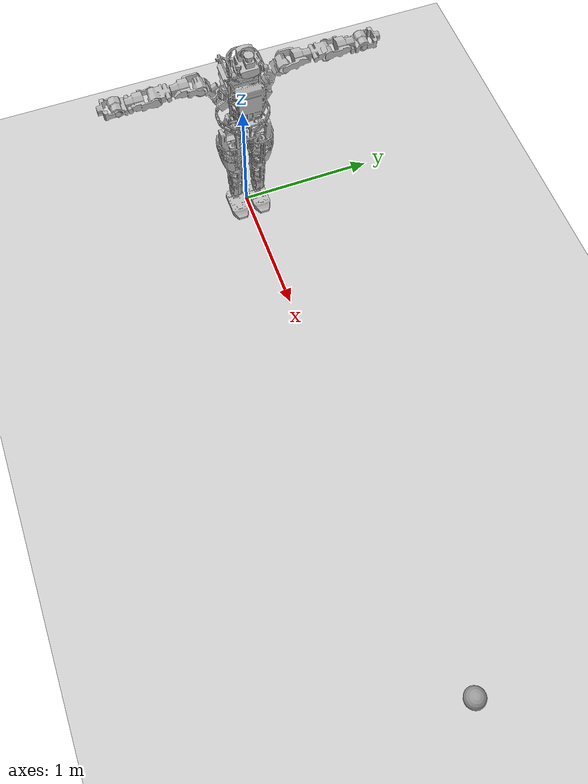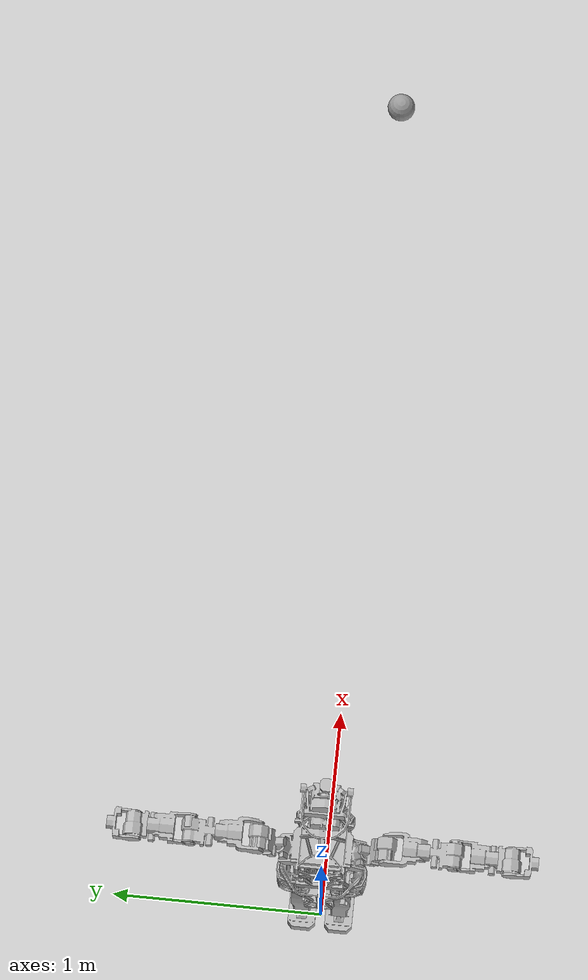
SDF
<sdf version='1.5'>
  <world name='default'>
    <gui fullscreen='0'>
      <camera name='user_camera'>
        <pose frame=''>1.47709 -5.36709 1.00889 0 -0 1.571</pose>
        <view_controller>orbit</view_controller>
      </camera>
    </gui>
    <physics name='default_physics' default='0' type='ode'>
      <gravity>0 0 -9.81</gravity>
      <simbody>
        <accuracy>0.005</accuracy>
        <max_transient_velocity>0.005</max_transient_velocity>
        <contact>
          <stiffness>1e+08</stiffness>
          <dissipation>20</dissipation>
        </contact>
      </simbody>
      <ode>
        <solver>
          <use_dynamic_moi_rescaling>1</use_dynamic_moi_rescaling>
          <type>quick</type>
          <iters>200</iters>
          <sor>1</sor>
        </solver>
        <constraints>
          <cfm>0</cfm>
          <erp>0.2</erp>
          <contact_max_correcting_vel>100</contact_max_correcting_vel>
          <contact_surface_layer>0</contact_surface_layer>
        </constraints>
      </ode>
      <real_time_update_rate>1000</real_time_update_rate>
      <max_step_size>0.001</max_step_size>
      <real_time_factor>1</real_time_factor>
      <magnetic_field>5.5645e-06 2.28758e-05 -4.23884e-05</magnetic_field>
    </physics>
    <light name='sun' type='directional'>
      <cast_shadows>1</cast_shadows>
      <pose frame=''>0 0 10 0 -0 0</pose>
      <diffuse>0.8 0.8 0.8 1</diffuse>
      <specular>0.2 0.2 0.2 1</specular>
      <attenuation>
        <range>1000</range>
        <constant>0.9</constant>
        <linear>0.01</linear>
        <quadratic>0.001</quadratic>
      </attenuation>
      <direction>-0.5 0.1 -0.9</direction>
    </light>
    <model name='ground_plane'>
      <static>1</static>
      <link name='link'>
        <collision name='collision'>
          <geometry>
            <plane>
              <normal>0 0 1</normal>
              <size>100 100</size>
            </plane>
          </geometry>
          <surface>
            <friction>
              <ode>
                <mu>100</mu>
                <mu2>50</mu2>
              </ode>
            </friction>
            <contact>
              <ode/>
            </contact>
            <bounce/>
          </surface>
          <max_contacts>10</max_contacts>
        </collision>
        <visual name='visual'>
          <cast_shadows>0</cast_shadows>
          <geometry>
            <plane>
              <normal>0 0 1</normal>
              <size>100 100</size>
            </plane>
          </geometry>
          <material>
            <script>
              <uri>file://media/materials/scripts/gazebo.material</uri>
              <name>Gazebo/Grey</name>
            </script>
          </material>
        </visual>
        <self_collide>0</self_collide>
        <kinematic>0</kinematic>
        <gravity>1</gravity>
      </link>
    </model>
    <model name='unit_sphere_1'>
      <plugin filename="libball_throwing.so" name="ball_throwing">
      </plugin>
      <pose frame=''>4 0 0.5 0 -0 0</pose>
      <link name='link'>
        <inertial>
          <mass>1</mass>
          <inertia>
            <ixx>1</ixx>
            <ixy>0</ixy>
            <ixz>0</ixz>
            <iyy>1</iyy>
            <iyz>0</iyz>
            <izz>1</izz>
          </inertia>
        </inertial>
        <collision name='collision'>
          <geometry>
            <sphere>
              <radius>0.0679466</radius>
            </sphere>
          </geometry>
          <max_contacts>10</max_contacts>
          <surface>
            <contact>
              <ode/>
            </contact>
            <bounce/>
            <friction>
              <ode/>
            </friction>
          </surface>
        </collision>
        <visual name='visual'>
          <geometry>
            <sphere>
              <radius>0.0679466</radius>
            </sphere>
          </geometry>
          <material>
            <script>
              <uri>file://media/materials/scripts/gazebo.material</uri>
              <name>Gazebo/Grey</name>
            </script>
          </material>
        </visual>
        <self_collide>0</self_collide>
        <kinematic>0</kinematic>
        <gravity>1</gravity>
      </link>
    </model>
    <plugin name='vrc_plugin' filename='libVRCPlugin.so'>
      <atlas>
        <model_name>atlas</model_name>
        <pin_link>utorso</pin_link>
      </atlas>
      <drc_vehicle>
        <model_name>golf_cart</model_name>
        <seat_link>chassis</seat_link>
      </drc_vehicle>
      <drc_fire_hose>
        <fire_hose_model>fire_hose</fire_hose_model>
        <coupling_link>coupling</coupling_link>
        <standpipe_model>standpipe</standpipe_model>
        <spout_link>standpipe</spout_link>
        <thread_pitch>-1000</thread_pitch>
        <coupling_relative_pose>1.17038e-05 -0.125623 0.35 -0.0412152 -1.57078 1.61199</coupling_relative_pose>
      </drc_fire_hose>
    </plugin>
    <plugin name='vrc_scoring' filename='libVRCScoringPlugin.so'/>
    <scene>
      <ambient>0.4 0.4 0.4 1</ambient>
      <background>0.7 0.7 0.7 1</background>
      <shadows>1</shadows>
    </scene>
    <spherical_coordinates>
      <surface_model>EARTH_WGS84</surface_model>
      <latitude_deg>0</latitude_deg>
      <longitude_deg>0</longitude_deg>
      <elevation>0</elevation>
      <heading_deg>0</heading_deg>
    </spherical_coordinates>
    <model name='atlas'>
      <link name='pelvis'>
        <pose frame=''>0 0 0 0 -0 0</pose>
        <inertial>
          <pose frame=''>0.0114401 0 0.0268126 0 -0 0</pose>
          <mass>14.3529</mass>
          <inertia>
            <ixx>0.125569</ixx>
            <ixy>0.0008</ixy>
            <ixz>-0.00050004</ixz>
            <iyy>0.0972056</iyy>
            <iyz>-0.0005</iyz>
            <izz>0.117937</izz>
          </inertia>
        </inertial>
        <collision name='pelvis_collision'>
          <pose frame=''>0.046 0 -0.02 1.5708 -0 0</pose>
          <geometry>
            <cylinder>
              <length>0.06</length>
              <radius>0.11</radius>
            </cylinder>
          </geometry>
          <surface>
            <contact>
              <ode/>
            </contact>
            <friction>
              <ode>
                <mu>0.9</mu>
                <mu2>0.9</mu2>
              </ode>
            </friction>
            <bounce/>
          </surface>
          <max_contacts>10</max_contacts>
        </collision>
        <collision name='pelvis_collision_pelvis_1'>
          <pose frame=''>-0.03 0 -0.02 1.5708 -0 0</pose>
          <geometry>
            <cylinder>
              <length>0.06</length>
              <radius>0.11</radius>
            </cylinder>
          </geometry>
          <surface>
            <contact>
              <ode/>
            </contact>
            <friction>
              <ode>
                <mu>0.9</mu>
                <mu2>0.9</mu2>
              </ode>
            </friction>
            <bounce/>
          </surface>
          <max_contacts>10</max_contacts>
        </collision>
        <collision name='pelvis_collision_pelvis_2'>
          <pose frame=''>0.01 0.042 0.09 0 -0 0</pose>
          <geometry>
            <cylinder>
              <length>0.05</length>
              <radius>0.16</radius>
            </cylinder>
          </geometry>
          <surface>
            <contact>
              <ode/>
            </contact>
            <friction>
              <ode>
                <mu>0.9</mu>
                <mu2>0.9</mu2>
              </ode>
            </friction>
            <bounce/>
          </surface>
          <max_contacts>10</max_contacts>
        </collision>
        <collision name='pelvis_collision_pelvis_3'>
          <pose frame=''>0.01 -0.042 0.09 0 -0 0</pose>
          <geometry>
            <cylinder>
              <length>0.05</length>
              <radius>0.16</radius>
            </cylinder>
          </geometry>
          <surface>
            <contact>
              <ode/>
            </contact>
            <friction>
              <ode>
                <mu>0.9</mu>
                <mu2>0.9</mu2>
              </ode>
            </friction>
            <bounce/>
          </surface>
          <max_contacts>10</max_contacts>
        </collision>
        <collision name='pelvis_collision_pelvis_4'>
          <pose frame=''>-0.1 0 -0.05 0 -0 0</pose>
          <geometry>
            <box>
              <size>0.1 0.15 0.2</size>
            </box>
          </geometry>
          <surface>
            <contact>
              <ode/>
            </contact>
            <friction>
              <ode>
                <mu>0.9</mu>
                <mu2>0.9</mu2>
              </ode>
            </friction>
            <bounce/>
          </surface>
          <max_contacts>10</max_contacts>
        </collision>
        <visual name='pelvis_visual'>
          <pose frame=''>0 0 0 0 -0 0</pose>
          <geometry>
            <mesh>
              <scale>1 1 1</scale>
              <uri>model://atlas_description/meshes/pelvis.dae</uri>
            </mesh>
          </geometry>
        </visual>
        <visual name='pelvis_visual_pelvis_1'>
          <pose frame=''>0.0599153 0 -0.01415 0 -0 0</pose>
          <geometry>
            <box>
              <size>0.01 0.01 0.01</size>
            </box>
          </geometry>
        </visual>
        <velocity_decay/>
        <gravity>1</gravity>
        <velocity_decay/>
        <self_collide>0</self_collide>
        <sensor name='imu_sensor' type='imu'>
          <always_on>1</always_on>
          <update_rate>1000</update_rate>
          <imu>
            <noise>
              <type>gaussian</type>
              <rate>
                <mean>0</mean>
                <stddev>0.0002</stddev>
                <bias_mean>7.5e-06</bias_mean>
                <bias_stddev>8e-07</bias_stddev>
              </rate>
              <accel>
                <mean>0</mean>
                <stddev>0.017</stddev>
                <bias_mean>0.1</bias_mean>
                <bias_stddev>0.001</bias_stddev>
              </accel>
            </noise>
          </imu>
          <pose frame=''>0.0599153 0 -0.01415 0 -0 0</pose>
        </sensor>
        <kinematic>0</kinematic>
      </link>
      <link name='ltorso'>
        <pose frame=''>-0.0125 0 0 0 -0 0</pose>
        <inertial>
          <pose frame=''>-0.0112984 -3.15366e-06 0.0746835 0 -0 0</pose>
          <mass>1.92</mass>
          <inertia>
            <ixx>0.0039092</ixx>
            <ixy>-5.04491e-08</ixy>
            <ixz>-0.000342157</ixz>
            <iyy>0.00341694</iyy>
            <iyz>4.87119e-07</iyz>
            <izz>0.00174492</izz>
          </inertia>
        </inertial>
        <visual name='ltorso_visual'>
          <pose frame=''>0 0 0 0 -0 0</pose>
          <geometry>
            <mesh>
              <scale>1 1 1</scale>
              <uri>model://atlas_description/meshes/ltorso.dae</uri>
            </mesh>
          </geometry>
        </visual>
        <gravity>1</gravity>
        <velocity_decay/>
        <self_collide>0</self_collide>
        <kinematic>0</kinematic>
      </link>
      <joint name='back_lbz' type='revolute'>
        <child>ltorso</child>
        <parent>pelvis</parent>
        <axis>
          <xyz>0 0 1</xyz>
          <limit>
            <lower>-0.610865</lower>
            <upper>0.610865</upper>
            <effort>124.016</effort>
            <velocity>12</velocity>
          </limit>
          <dynamics>
            <damping>10</damping>
            <friction>0</friction>
            <spring_reference>0</spring_reference>
            <spring_stiffness>0</spring_stiffness>
          </dynamics>
          <use_parent_model_frame>1</use_parent_model_frame>
        </axis>
        <physics>
          <ode>
            <implicit_spring_damper>1</implicit_spring_damper>
            <cfm_damping>1</cfm_damping>
            <limit>
              <cfm>0</cfm>
              <erp>0.2</erp>
            </limit>
          </ode>
        </physics>
      </joint>
      <link name='mtorso'>
        <pose frame=''>-0.0125 0 0.09 0 -0 0</pose>
        <inertial>
          <pose frame=''>-0.00816266 -0.0131245 0.0305974 0 -0 0</pose>
          <mass>0.55</mass>
          <inertia>
            <ixx>0.000454181</ixx>
            <ixy>-6.10764e-05</ixy>
            <ixz>3.94009e-05</ixz>
            <iyy>0.000483282</iyy>
            <iyz>5.27463e-05</iyz>
            <izz>0.000444215</izz>
          </inertia>
        </inertial>
        <collision name='mtorso_collision'>
          <pose frame=''>0 0 0 1.5708 -0 0</pose>
          <geometry>
            <cylinder>
              <length>0.03</length>
              <radius>0.017</radius>
            </cylinder>
          </geometry>
          <surface>
            <contact>
              <ode/>
            </contact>
            <friction>
              <ode>
                <mu>0.9</mu>
                <mu2>0.9</mu2>
              </ode>
            </friction>
            <bounce/>
          </surface>
          <max_contacts>10</max_contacts>
        </collision>
        <collision name='mtorso_collision_mtorso_1'>
          <pose frame=''>0.0285 0 0.05 -2.65359e-06 1.57079 -2.65359e-06</pose>
          <geometry>
            <cylinder>
              <length>0.02</length>
              <radius>0.015</radius>
            </cylinder>
          </geometry>
          <surface>
            <contact>
              <ode/>
            </contact>
            <friction>
              <ode>
                <mu>0.9</mu>
                <mu2>0.9</mu2>
              </ode>
            </friction>
            <bounce/>
          </surface>
          <max_contacts>10</max_contacts>
        </collision>
        <collision name='mtorso_collision_mtorso_2'>
          <pose frame=''>-0.0285 0 0.05 -2.65359e-06 1.57079 -2.65359e-06</pose>
          <geometry>
            <cylinder>
              <length>0.02</length>
              <radius>0.015</radius>
            </cylinder>
          </geometry>
          <surface>
            <contact>
              <ode/>
            </contact>
            <friction>
              <ode>
                <mu>0.9</mu>
                <mu2>0.9</mu2>
              </ode>
            </friction>
            <bounce/>
          </surface>
          <max_contacts>10</max_contacts>
        </collision>
        <visual name='mtorso_visual'>
          <pose frame=''>0 0 0 0 -0 0</pose>
          <geometry>
            <mesh>
              <scale>1 1 1</scale>
              <uri>model://atlas_description/meshes/mtorso.dae</uri>
            </mesh>
          </geometry>
        </visual>
        <gravity>1</gravity>
        <velocity_decay/>
        <self_collide>0</self_collide>
        <kinematic>0</kinematic>
      </link>
      <joint name='back_mby' type='revolute'>
        <child>mtorso</child>
        <parent>ltorso</parent>
        <axis>
          <xyz>0 1 0</xyz>
          <limit>
            <lower>-1.2</lower>
            <upper>1.28</upper>
            <effort>206.843</effort>
            <velocity>12</velocity>
          </limit>
          <dynamics>
            <damping>10</damping>
            <friction>0</friction>
            <spring_reference>0</spring_reference>
            <spring_stiffness>0</spring_stiffness>
          </dynamics>
          <use_parent_model_frame>1</use_parent_model_frame>
        </axis>
        <physics>
          <ode>
            <implicit_spring_damper>1</implicit_spring_damper>
            <cfm_damping>1</cfm_damping>
            <limit>
              <cfm>0</cfm>
              <erp>0.2</erp>
            </limit>
          </ode>
        </physics>
      </joint>
      <link name='utorso'>
        <pose frame=''>-0.0125 0 0.14 0 -0 0</pose>
        <inertial>
          <pose frame=''>0.02 -0.001 0.211 0 -0 0</pose>
          <mass>18.484</mass>
          <inertia>
            <ixx>0.395</ixx>
            <ixy>0</ixy>
            <ixz>0.083</ixz>
            <iyy>1.089</iyy>
            <iyz>-0.003</iyz>
            <izz>0.827</izz>
          </inertia>
        </inertial>
        <collision name='utorso_collision'>
          <pose frame=''>0.0446 0 0.1869 0 -0 0</pose>
          <geometry>
            <box>
              <size>0.3188 0.24 0.3162</size>
            </box>
          </geometry>
          <surface>
            <contact>
              <ode/>
            </contact>
            <friction>
              <ode>
                <mu>0.9</mu>
                <mu2>0.9</mu2>
              </ode>
            </friction>
            <bounce/>
          </surface>
          <max_contacts>10</max_contacts>
        </collision>
        <collision name='utorso_collision_utorso_1'>
          <pose frame=''>0.024 0.16 0.18 -0.5236 0 0</pose>
          <geometry>
            <cylinder>
              <length>0.22375</length>
              <radius>0.0363</radius>
            </cylinder>
          </geometry>
          <surface>
            <contact>
              <ode/>
            </contact>
            <friction>
              <ode>
                <mu>0.9</mu>
                <mu2>0.9</mu2>
              </ode>
            </friction>
            <bounce/>
          </surface>
          <max_contacts>10</max_contacts>
        </collision>
        <collision name='utorso_collision_utorso_2'>
          <pose frame=''>0.024 -0.16 0.18 0.5236 -0 0</pose>
          <geometry>
            <cylinder>
              <length>0.22375</length>
              <radius>0.0363</radius>
            </cylinder>
          </geometry>
          <surface>
            <contact>
              <ode/>
            </contact>
            <friction>
              <ode>
                <mu>0.9</mu>
                <mu2>0.9</mu2>
              </ode>
            </friction>
            <bounce/>
          </surface>
          <max_contacts>10</max_contacts>
        </collision>
        <visual name='utorso_visual'>
          <pose frame=''>0 0 0 0 -0 0</pose>
          <geometry>
            <mesh>
              <scale>1 1 1</scale>
              <uri>model://atlas_description/meshes/utorso.dae</uri>
            </mesh>
          </geometry>
        </visual>
        <gravity>1</gravity>
        <velocity_decay/>
        <self_collide>0</self_collide>
        <kinematic>0</kinematic>
      </link>
      <joint name='back_ubx' type='revolute'>
        <child>utorso</child>
        <parent>mtorso</parent>
        <axis>
          <xyz>1 0 0</xyz>
          <limit>
            <lower>-0.790809</lower>
            <upper>0.790809</upper>
            <effort>94.91</effort>
            <velocity>12</velocity>
          </limit>
          <dynamics>
            <damping>10</damping>
            <friction>0</friction>
            <spring_reference>0</spring_reference>
            <spring_stiffness>0</spring_stiffness>
          </dynamics>
          <use_parent_model_frame>1</use_parent_model_frame>
        </axis>
        <physics>
          <ode>
            <implicit_spring_damper>1</implicit_spring_damper>
            <cfm_damping>1</cfm_damping>
            <limit>
              <cfm>0</cfm>
              <erp>0.2</erp>
            </limit>
          </ode>
        </physics>
      </joint>
      <link name='l_clav'>
        <pose frame=''>0.0115 0.221 0.429 0 -0 0</pose>
        <inertial>
          <pose frame=''>0.014 0.058 0.029 0 -0 0</pose>
          <mass>2.369</mass>
          <inertia>
            <ixx>0.004</ixx>
            <ixy>0.001</ixy>
            <ixz>0</ixz>
            <iyy>0.006</iyy>
            <iyz>0</iyz>
            <izz>0.007</izz>
          </inertia>
        </inertial>
        <collision name='l_clav_collision'>
          <pose frame=''>0 0.0697 0.0261 -2.65359e-06 1.57079 -2.65359e-06</pose>
          <geometry>
            <cylinder>
              <length>0.1525</length>
              <radius>0.045</radius>
            </cylinder>
          </geometry>
          <surface>
            <contact>
              <ode/>
            </contact>
            <friction>
              <ode>
                <mu>0.9</mu>
                <mu2>0.9</mu2>
              </ode>
            </friction>
            <bounce/>
          </surface>
          <max_contacts>10</max_contacts>
        </collision>
        <collision name='l_clav_collision_l_clav_1'>
          <pose frame=''>-0.005 -0.0074 -0.0538 1.0472 -0 0</pose>
          <geometry>
            <box>
              <size>0.13 0.15 0.05</size>
            </box>
          </geometry>
          <surface>
            <contact>
              <ode/>
            </contact>
            <friction>
              <ode>
                <mu>0.9</mu>
                <mu2>0.9</mu2>
              </ode>
            </friction>
            <bounce/>
          </surface>
          <max_contacts>10</max_contacts>
        </collision>
        <visual name='l_clav_visual'>
          <pose frame=''>0 0 0 1.0472 -0 0</pose>
          <geometry>
            <mesh>
              <scale>1 1 1</scale>
              <uri>model://atlas_description/meshes/l_clav.dae</uri>
            </mesh>
          </geometry>
        </visual>
        <gravity>1</gravity>
        <velocity_decay/>
        <self_collide>0</self_collide>
        <kinematic>0</kinematic>
      </link>
      <joint name='l_arm_usy' type='revolute'>
        <child>l_clav</child>
        <parent>utorso</parent>
        <axis>
          <xyz>0 0.5 0.866025</xyz>
          <limit>
            <lower>-1.9635</lower>
            <upper>1.9635</upper>
            <effort>212</effort>
            <velocity>12</velocity>
          </limit>
          <dynamics>
            <damping>1</damping>
            <friction>0</friction>
            <spring_reference>0</spring_reference>
            <spring_stiffness>0</spring_stiffness>
          </dynamics>
          <use_parent_model_frame>1</use_parent_model_frame>
        </axis>
        <physics>
          <ode>
            <implicit_spring_damper>1</implicit_spring_damper>
            <cfm_damping>1</cfm_damping>
            <limit>
              <cfm>0</cfm>
              <erp>0.2</erp>
            </limit>
          </ode>
        </physics>
      </joint>
      <link name='l_scap'>
        <pose frame=''>0.0115 0.296 0.465 0 -0 0</pose>
        <inertial>
          <pose frame=''>-0.002 0.108 0 0 -0 0</pose>
          <mass>2.707</mass>
          <inertia>
            <ixx>0.01</ixx>
            <ixy>0</ixy>
            <ixz>0</ixz>
            <iyy>0.005</iyy>
            <iyz>0</iyz>
            <izz>0.013</izz>
          </inertia>
        </inertial>
        <collision name='l_scap_collision'>
          <pose frame=''>0.001 0.12651 0.01521 1.5708 -0 0</pose>
          <geometry>
            <cylinder>
              <length>0.125</length>
              <radius>0.045</radius>
            </cylinder>
          </geometry>
          <surface>
            <contact>
              <ode/>
            </contact>
            <friction>
              <ode>
                <mu>0.9</mu>
                <mu2>0.9</mu2>
              </ode>
            </friction>
            <bounce/>
          </surface>
          <max_contacts>10</max_contacts>
        </collision>
        <collision name='l_scap_collision_l_scap_1'>
          <pose frame=''>0.001 0.05 0.016 0 -0 0</pose>
          <geometry>
            <box>
              <size>0.15 0.15 0.06</size>
            </box>
          </geometry>
          <surface>
            <contact>
              <ode/>
            </contact>
            <friction>
              <ode>
                <mu>0.9</mu>
                <mu2>0.9</mu2>
              </ode>
            </friction>
            <bounce/>
          </surface>
          <max_contacts>10</max_contacts>
        </collision>
        <visual name='l_scap_visual'>
          <pose frame=''>0 0 0 0 -0 0</pose>
          <geometry>
            <mesh>
              <scale>1 1 1</scale>
              <uri>model://atlas_description/meshes/l_scap.dae</uri>
            </mesh>
          </geometry>
        </visual>
        <gravity>1</gravity>
        <velocity_decay/>
        <self_collide>0</self_collide>
        <kinematic>0</kinematic>
      </link>
      <joint name='l_arm_shx' type='revolute'>
        <child>l_scap</child>
        <parent>l_clav</parent>
        <axis>
          <xyz>1 0 0</xyz>
          <limit>
            <lower>-1.39626</lower>
            <upper>1.74533</upper>
            <effort>170</effort>
            <velocity>12</velocity>
          </limit>
          <dynamics>
            <damping>1</damping>
            <friction>0</friction>
            <spring_reference>0</spring_reference>
            <spring_stiffness>0</spring_stiffness>
          </dynamics>
          <use_parent_model_frame>1</use_parent_model_frame>
        </axis>
        <physics>
          <ode>
            <implicit_spring_damper>1</implicit_spring_damper>
            <cfm_damping>1</cfm_damping>
            <limit>
              <cfm>0</cfm>
              <erp>0.2</erp>
            </limit>
          </ode>
        </physics>
      </joint>
      <link name='l_uarm'>
        <pose frame=''>0.0115 0.481 0.465 0 -0 0</pose>
        <inertial>
          <pose frame=''>0.007 0.114 0.008 0 -0 0</pose>
          <mass>1.881</mass>
          <inertia>
            <ixx>0.002</ixx>
            <ixy>0</ixy>
            <ixz>0</ixz>
            <iyy>0.003</iyy>
            <iyz>0</iyz>
            <izz>0.003</izz>
          </inertia>
        </inertial>
        <collision name='l_uarm_collision'>
          <pose frame=''>0.001 0.111 0 3.14159 1.57079 3.14159</pose>
          <geometry>
            <cylinder>
              <length>0.125</length>
              <radius>0.045</radius>
            </cylinder>
          </geometry>
          <surface>
            <contact>
              <ode/>
            </contact>
            <friction>
              <ode>
                <mu>0.9</mu>
                <mu2>0.9</mu2>
              </ode>
            </friction>
            <bounce/>
          </surface>
          <max_contacts>10</max_contacts>
        </collision>
        <collision name='l_uarm_collision_l_uarm_1'>
          <pose frame=''>0.001 0.043 0.01 -2.65359e-06 1.57079 -2.65359e-06</pose>
          <geometry>
            <box>
              <size>0.04 0.07 0.13</size>
            </box>
          </geometry>
          <surface>
            <contact>
              <ode/>
            </contact>
            <friction>
              <ode>
                <mu>0.9</mu>
                <mu2>0.9</mu2>
              </ode>
            </friction>
            <bounce/>
          </surface>
          <max_contacts>10</max_contacts>
        </collision>
        <visual name='l_uarm_visual'>
          <pose frame=''>0 0 0 0 -0 0</pose>
          <geometry>
            <mesh>
              <scale>1 1 1</scale>
              <uri>model://atlas_description/meshes/l_uarm.dae</uri>
            </mesh>
          </geometry>
        </visual>
        <gravity>1</gravity>
        <velocity_decay/>
        <self_collide>0</self_collide>
        <kinematic>0</kinematic>
      </link>
      <joint name='l_arm_ely' type='revolute'>
        <child>l_uarm</child>
        <parent>l_scap</parent>
        <axis>
          <xyz>0 1 0</xyz>
          <limit>
            <lower>0</lower>
            <upper>3.14159</upper>
            <effort>114</effort>
            <velocity>12</velocity>
          </limit>
          <dynamics>
            <damping>1</damping>
            <friction>0</friction>
            <spring_reference>0</spring_reference>
            <spring_stiffness>0</spring_stiffness>
          </dynamics>
          <use_parent_model_frame>1</use_parent_model_frame>
        </axis>
        <physics>
          <ode>
            <implicit_spring_damper>1</implicit_spring_damper>
            <cfm_damping>1</cfm_damping>
            <limit>
              <cfm>0</cfm>
              <erp>0.2</erp>
            </limit>
          </ode>
        </physics>
      </joint>
      <link name='l_larm'>
        <pose frame=''>0.0115 0.602 0.478 0 -0 0</pose>
        <inertial>
          <pose frame=''>-0.003 0.099 -0.014 0 -0 0</pose>
          <mass>2.148</mass>
          <inertia>
            <ixx>0.005</ixx>
            <ixy>0</ixy>
            <ixz>0</ixz>
            <iyy>0.003</iyy>
            <iyz>0</iyz>
            <izz>0.006</izz>
          </inertia>
        </inertial>
        <collision name='l_larm_collision'>
          <pose frame=''>0.001 0.127 0 1.5708 -0 0</pose>
          <geometry>
            <cylinder>
              <length>0.125</length>
              <radius>0.045</radius>
            </cylinder>
          </geometry>
          <surface>
            <contact>
              <ode/>
            </contact>
            <friction>
              <ode>
                <mu>0.9</mu>
                <mu2>0.9</mu2>
              </ode>
            </friction>
            <bounce/>
          </surface>
          <max_contacts>10</max_contacts>
        </collision>
        <collision name='l_larm_collision_l_larm_1'>
          <pose frame=''>0.001 0.051 0 0 -0 0</pose>
          <geometry>
            <box>
              <size>0.135 0.15 0.06</size>
            </box>
          </geometry>
          <surface>
            <contact>
              <ode/>
            </contact>
            <friction>
              <ode>
                <mu>0.9</mu>
                <mu2>0.9</mu2>
              </ode>
            </friction>
            <bounce/>
          </surface>
          <max_contacts>10</max_contacts>
        </collision>
        <visual name='l_larm_visual'>
          <pose frame=''>0 0 0 0 -0 0</pose>
          <geometry>
            <mesh>
              <scale>1 1 1</scale>
              <uri>model://atlas_description/meshes/l_larm.dae</uri>
            </mesh>
          </geometry>
        </visual>
        <gravity>1</gravity>
        <velocity_decay/>
        <self_collide>0</self_collide>
        <kinematic>0</kinematic>
      </link>
      <joint name='l_arm_elx' type='revolute'>
        <child>l_larm</child>
        <parent>l_uarm</parent>
        <axis>
          <xyz>1 0 0</xyz>
          <limit>
            <lower>0</lower>
            <upper>2.35619</upper>
            <effort>114</effort>
            <velocity>12</velocity>
          </limit>
          <dynamics>
            <damping>1</damping>
            <friction>0</friction>
            <spring_reference>0</spring_reference>
            <spring_stiffness>0</spring_stiffness>
          </dynamics>
          <use_parent_model_frame>1</use_parent_model_frame>
        </axis>
        <physics>
          <ode>
            <implicit_spring_damper>1</implicit_spring_damper>
            <cfm_damping>1</cfm_damping>
            <limit>
              <cfm>0</cfm>
              <erp>0.2</erp>
            </limit>
          </ode>
        </physics>
      </joint>
      <link name='l_farm'>
        <pose frame=''>0.0115 0.79 0.465 0 -0 0</pose>
        <inertial>
          <pose frame=''>0 0.041 0 0 -0 0</pose>
          <mass>0.981</mass>
          <inertia>
            <ixx>0.003</ixx>
            <ixy>0</ixy>
            <ixz>0</ixz>
            <iyy>0.001</iyy>
            <iyz>0</iyz>
            <izz>0.003</izz>
          </inertia>
        </inertial>
        <collision name='l_farm_collision'>
          <pose frame=''>0 0.065 0.004 3.14159 1.57079 3.14159</pose>
          <geometry>
            <cylinder>
              <length>0.125</length>
              <radius>0.045</radius>
            </cylinder>
          </geometry>
          <surface>
            <contact>
              <ode/>
            </contact>
            <friction>
              <ode>
                <mu>0.9</mu>
                <mu2>0.9</mu2>
              </ode>
            </friction>
            <bounce/>
          </surface>
          <max_contacts>10</max_contacts>
        </collision>
        <collision name='l_farm_collision_l_farm_1'>
          <pose frame=''>0.001 0.015 -0.002 0 -0 0</pose>
          <geometry>
            <box>
              <size>0.135 0.1 0.045</size>
            </box>
          </geometry>
          <surface>
            <contact>
              <ode/>
            </contact>
            <friction>
              <ode>
                <mu>0.9</mu>
                <mu2>0.9</mu2>
              </ode>
            </friction>
            <bounce/>
          </surface>
          <max_contacts>10</max_contacts>
        </collision>
        <visual name='l_farm_visual'>
          <pose frame=''>0 -0.06 0 0 -0 0</pose>
          <geometry>
            <mesh>
              <scale>1 1 1</scale>
              <uri>model://atlas_description/meshes/l_farm.dae</uri>
            </mesh>
          </geometry>
        </visual>
        <gravity>1</gravity>
        <velocity_decay/>
        <self_collide>0</self_collide>
        <kinematic>0</kinematic>
      </link>
      <joint name='l_arm_uwy' type='revolute'>
        <child>l_farm</child>
        <parent>l_larm</parent>
        <axis>
          <xyz>0 1 0</xyz>
          <limit>
            <lower>-1.571</lower>
            <upper>1.571</upper>
            <effort>114</effort>
            <velocity>12</velocity>
          </limit>
          <dynamics>
            <damping>1</damping>
            <friction>0</friction>
            <spring_reference>0</spring_reference>
            <spring_stiffness>0</spring_stiffness>
          </dynamics>
          <use_parent_model_frame>1</use_parent_model_frame>
        </axis>
        <physics>
          <ode>
            <implicit_spring_damper>1</implicit_spring_damper>
            <cfm_damping>1</cfm_damping>
            <limit>
              <cfm>0</cfm>
              <erp>0.2</erp>
            </limit>
          </ode>
        </physics>
      </joint>
      <link name='l_hand'>
        <pose frame=''>0.0115 0.848 0.465 0 -0 0</pose>
        <inertial>
          <pose frame=''>0 0.093 0 0 -0 0</pose>
          <mass>2.263</mass>
          <inertia>
            <ixx>0.01</ixx>
            <ixy>0</ixy>
            <ixz>0</ixz>
            <iyy>0.002</iyy>
            <iyz>0</iyz>
            <izz>0.01</izz>
          </inertia>
        </inertial>
        <collision name='l_hand_collision'>
          <pose frame=''>0.001 0.1 0.01 1.5708 -0 0</pose>
          <geometry>
            <cylinder>
              <length>0.05</length>
              <radius>0.03</radius>
            </cylinder>
          </geometry>
          <surface>
            <contact>
              <ode/>
            </contact>
            <friction>
              <ode>
                <mu>0.9</mu>
                <mu2>0.9</mu2>
              </ode>
            </friction>
            <bounce/>
          </surface>
          <max_contacts>10</max_contacts>
        </collision>
        <collision name='l_hand_collision_l_hand_1'>
          <pose frame=''>0.001 0.05 0.01 0 -0 0</pose>
          <geometry>
            <box>
              <size>0.13 0.09 0.07</size>
            </box>
          </geometry>
          <surface>
            <contact>
              <ode/>
            </contact>
            <friction>
              <ode>
                <mu>0.9</mu>
                <mu2>0.9</mu2>
              </ode>
            </friction>
            <bounce/>
          </surface>
          <max_contacts>10</max_contacts>
        </collision>
        <visual name='l_hand_visual'>
          <pose frame=''>0 0 0 0 -0 0</pose>
          <geometry>
            <mesh>
              <scale>1 1 1</scale>
              <uri>model://atlas_description/meshes/l_hand.dae</uri>
            </mesh>
          </geometry>
        </visual>
        <gravity>1</gravity>
        <velocity_decay/>
        <self_collide>0</self_collide>
        <kinematic>0</kinematic>
      </link>
      <joint name='l_arm_mwx' type='revolute'>
        <child>l_hand</child>
        <parent>l_farm</parent>
        <axis>
          <xyz>1 0 0</xyz>
          <limit>
            <lower>-0.436</lower>
            <upper>1.571</upper>
            <effort>60</effort>
            <velocity>12</velocity>
          </limit>
          <dynamics>
            <damping>1</damping>
            <friction>0</friction>
            <spring_reference>0</spring_reference>
            <spring_stiffness>0</spring_stiffness>
          </dynamics>
          <use_parent_model_frame>1</use_parent_model_frame>
        </axis>
        <physics>
          <provide_feedback>1</provide_feedback>
          <ode>
            <provide_feedback>1</provide_feedback>
            <limit>
              <cfm>0</cfm>
              <erp>0.2</erp>
            </limit>
            <implicit_spring_damper>1</implicit_spring_damper>
            <cfm_damping>1</cfm_damping>
          </ode>
        </physics>
      </joint>
      <link name='head'>
        <pose frame=''>0.20422 0 0.67796 0 -0 0</pose>
        <inertial>
          <pose frame=''>-0.0754942 3.38765e-05 0.0277411 0 -0 0</pose>
          <mass>1.41991</mass>
          <inertia>
            <ixx>0.00397627</ixx>
            <ixy>-1.51324e-06</ixy>
            <ixz>-0.000892818</ixz>
            <iyy>0.00412515</iyy>
            <iyz>-6.83342e-07</iyz>
            <izz>0.00353178</izz>
          </inertia>
        </inertial>
        <collision name='head_collision'>
          <pose frame=''>-0.0503 0 -0.00195 0 -0 0</pose>
          <geometry>
            <box>
              <size>0.1311 0.12 0.0591</size>
            </box>
          </geometry>
          <surface>
            <contact>
              <ode/>
            </contact>
            <friction>
              <ode>
                <mu>0.9</mu>
                <mu2>0.9</mu2>
              </ode>
            </friction>
            <bounce/>
          </surface>
          <max_contacts>10</max_contacts>
        </collision>
        <collision name='head_collision_head_1'>
          <pose frame=''>-0.093 0 0.0868 0 -0 0</pose>
          <geometry>
            <box>
              <size>0.0468 0.12 0.1184</size>
            </box>
          </geometry>
          <surface>
            <contact>
              <ode/>
            </contact>
            <friction>
              <ode>
                <mu>0.9</mu>
                <mu2>0.9</mu2>
              </ode>
            </friction>
            <bounce/>
          </surface>
          <max_contacts>10</max_contacts>
        </collision>
        <visual name='head_visual'>
          <pose frame=''>0 0 0 0 -0 0</pose>
          <geometry>
            <mesh>
              <scale>1 1 1</scale>
              <uri>model://multisense_sl_description/meshes/head.dae</uri>
            </mesh>
          </geometry>
        </visual>
        <visual name='head_visual_head_1'>
          <pose frame=''>-0.0475 0.035 0 0 -0 0</pose>
          <geometry>
            <box>
              <size>0.01 0.01 0.01</size>
            </box>
          </geometry>
        </visual>
        <velocity_decay/>
        <velocity_decay/>
        <sensor name='head_imu_sensor' type='imu'>
          <always_on>1</always_on>
          <update_rate>1000</update_rate>
          <imu>
            <noise>
              <type>gaussian</type>
              <rate>
                <mean>0</mean>
                <stddev>0.0002</stddev>
                <bias_mean>7.5e-06</bias_mean>
                <bias_stddev>8e-07</bias_stddev>
              </rate>
              <accel>
                <mean>0</mean>
                <stddev>0.017</stddev>
                <bias_mean>0.1</bias_mean>
                <bias_stddev>0.001</bias_stddev>
              </accel>
            </noise>
          </imu>
          <pose frame=''>-0.0475 0.035 0 0 -0 0</pose>
        </sensor>
        <gravity>1</gravity>
        <velocity_decay/>
        <self_collide>0</self_collide>
        <sensor name='stereo_camera' type='multicamera'>
          <update_rate>30</update_rate>
          <camera name='left'>
            <horizontal_fov>1.39626</horizontal_fov>
            <image>
              <width>800</width>
              <height>800</height>
              <format>R8G8B8</format>
            </image>
            <clip>
              <near>0.02</near>
              <far>300</far>
            </clip>
            <noise>
              <type>gaussian</type>
              <mean>0</mean>
              <stddev>0.007</stddev>
            </noise>
          </camera>
          <camera name='right'>
            <pose frame=''>0 -0.07 0 0 -0 0</pose>
            <horizontal_fov>1.39626</horizontal_fov>
            <image>
              <width>800</width>
              <height>800</height>
              <format>R8G8B8</format>
            </image>
            <clip>
              <near>0.02</near>
              <far>300</far>
            </clip>
            <noise>
              <type>gaussian</type>
              <mean>0</mean>
              <stddev>0.007</stddev>
            </noise>
          </camera>
          <plugin name='stereo_camera_controller' filename='libgazebo_ros_multicamera.so'>
            <alwaysOn>true</alwaysOn>
            <updateRate>0.0</updateRate>
            <cameraName>multisense_sl</cameraName>
            <imageTopicName>image_raw</imageTopicName>
            <cameraInfoTopicName>camera_info</cameraInfoTopicName>
            <frameName>left_camera_optical_frame</frameName>
            <hackBaseline>0.07</hackBaseline>
            <distortionK1>0.0</distortionK1>
            <distortionK2>0.0</distortionK2>
            <distortionK3>0.0</distortionK3>
            <distortionT1>0.0</distortionT1>
            <distortionT2>0.0</distortionT2>
          </plugin>
          <pose frame=''>0 0.035 -0.002 0 -0 0</pose>
        </sensor>
        <kinematic>0</kinematic>
      </link>
      <joint name='neck_ay' type='revolute'>
        <child>head</child>
        <parent>utorso</parent>
        <axis>
          <xyz>0 1 0</xyz>
          <limit>
            <lower>-0.610865</lower>
            <upper>1.13446</upper>
            <effort>5</effort>
            <velocity>12</velocity>
          </limit>
          <dynamics>
            <damping>1</damping>
            <friction>0</friction>
            <spring_reference>0</spring_reference>
            <spring_stiffness>0</spring_stiffness>
          </dynamics>
          <use_parent_model_frame>1</use_parent_model_frame>
        </axis>
        <physics>
          <ode>
            <implicit_spring_damper>1</implicit_spring_damper>
            <cfm_damping>1</cfm_damping>
            <limit>
              <cfm>0</cfm>
              <erp>0.2</erp>
            </limit>
          </ode>
        </physics>
      </joint>
      <link name='hokuyo_link'>
        <pose frame=''>0.15962 0 0.76596 0 -0 0</pose>
        <inertial>
          <pose frame=''>0.0324349 0.0004084 -0.0041783 0 -0 0</pose>
          <mass>0.057664</mass>
          <inertia>
            <ixx>3.8183e-05</ixx>
            <ixy>4.9927e-08</ixy>
            <ixz>1.1003e-05</ixz>
            <iyy>4.3437e-05</iyy>
            <iyz>-9.8165e-09</iyz>
            <izz>4.2686e-05</izz>
          </inertia>
        </inertial>
        <collision name='hokuyo_link_collision'>
          <pose frame=''>0.01885 0 -0.02119 0 -0 0</pose>
          <geometry>
            <box>
              <size>0.08 0.06 0.04238</size>
            </box>
          </geometry>
          <surface>
            <contact>
              <ode/>
            </contact>
            <friction>
              <ode>
                <mu>0.9</mu>
                <mu2>0.9</mu2>
              </ode>
            </friction>
            <bounce/>
          </surface>
          <max_contacts>10</max_contacts>
        </collision>
        <collision name='hokuyo_link_collision_hokuyo_link_1'>
          <pose frame=''>0.03 0 0.0235 0 -0 0</pose>
          <geometry>
            <cylinder>
              <length>0.047</length>
              <radius>0.024425</radius>
            </cylinder>
          </geometry>
          <surface>
            <contact>
              <ode/>
            </contact>
            <friction>
              <ode>
                <mu>0.9</mu>
                <mu2>0.9</mu2>
              </ode>
            </friction>
            <bounce/>
          </surface>
          <max_contacts>10</max_contacts>
        </collision>
        <visual name='hokuyo_link_visual'>
          <pose frame=''>0.045 -0.0261018 -0.0834237 -0.314 0 0</pose>
          <geometry>
            <mesh>
              <scale>1 1 1</scale>
              <uri>model://multisense_sl_description/meshes/head_camera.dae</uri>
            </mesh>
          </geometry>
        </visual>
        <velocity_decay/>
        <gravity>1</gravity>
        <velocity_decay/>
        <self_collide>0</self_collide>
        <sensor name='head_hokuyo_sensor' type='gpu_ray'>
          <visualize>0</visualize>
          <update_rate>40</update_rate>
          <ray>
            <scan>
              <horizontal>
                <samples>720</samples>
                <resolution>1</resolution>
                <min_angle>-1.5708</min_angle>
                <max_angle>1.5708</max_angle>
              </horizontal>
            </scan>
            <range>
              <min>0.1</min>
              <max>30</max>
              <resolution>0.01</resolution>
            </range>
            <noise>
              <type>gaussian</type>
              <mean>0</mean>
              <stddev>0.01</stddev>
            </noise>
          </ray>
          <plugin name='gazebo_ros_head_hokuyo_controller' filename='libgazebo_ros_gpu_laser.so'>
            <topicName>/laser/scan</topicName>
            <frameName>head_hokuyo_frame</frameName>
          </plugin>
          <pose frame=''>0.03 0 0.015 0 -0 0</pose>
        </sensor>
        <kinematic>0</kinematic>
      </link>
      <joint name='hokuyo_joint' type='revolute'>
        <child>hokuyo_link</child>
        <parent>head</parent>
        <axis>
          <xyz>1 0 0</xyz>
          <limit>
            <lower>-1e+16</lower>
            <upper>1e+16</upper>
          </limit>
          <dynamics>
            <damping>0.01</damping>
            <friction>0</friction>
            <spring_reference>0</spring_reference>
            <spring_stiffness>0</spring_stiffness>
          </dynamics>
          <use_parent_model_frame>1</use_parent_model_frame>
        </axis>
        <physics>
          <ode>
            <implicit_spring_damper>1</implicit_spring_damper>
            <cfm_damping>1</cfm_damping>
            <limit>
              <cfm>0</cfm>
              <erp>0.2</erp>
            </limit>
          </ode>
        </physics>
      </joint>
      <link name='r_clav'>
        <pose frame=''>0.0115 -0.221 0.429 0 -0 0</pose>
        <inertial>
          <pose frame=''>0.014 -0.058 0.029 0 -0 0</pose>
          <mass>2.369</mass>
          <inertia>
            <ixx>0.004</ixx>
            <ixy>-0.001</ixy>
            <ixz>0</ixz>
            <iyy>0.006</iyy>
            <iyz>0</iyz>
            <izz>0.007</izz>
          </inertia>
        </inertial>
        <collision name='r_clav_collision'>
          <pose frame=''>0 -0.0697 0.0261 -2.65359e-06 1.57079 -2.65359e-06</pose>
          <geometry>
            <cylinder>
              <length>0.1525</length>
              <radius>0.045</radius>
            </cylinder>
          </geometry>
          <surface>
            <contact>
              <ode/>
            </contact>
            <friction>
              <ode>
                <mu>0.9</mu>
                <mu2>0.9</mu2>
              </ode>
            </friction>
            <bounce/>
          </surface>
          <max_contacts>10</max_contacts>
        </collision>
        <collision name='r_clav_collision_r_clav_1'>
          <pose frame=''>-0.005 0.0074 -0.0538 -1.0472 0 0</pose>
          <geometry>
            <box>
              <size>0.13 0.15 0.05</size>
            </box>
          </geometry>
          <surface>
            <contact>
              <ode/>
            </contact>
            <friction>
              <ode>
                <mu>0.9</mu>
                <mu2>0.9</mu2>
              </ode>
            </friction>
            <bounce/>
          </surface>
          <max_contacts>10</max_contacts>
        </collision>
        <visual name='r_clav_visual'>
          <pose frame=''>0 0 0 -1.0472 0 0</pose>
          <geometry>
            <mesh>
              <scale>1 1 1</scale>
              <uri>model://atlas_description/meshes/r_clav.dae</uri>
            </mesh>
          </geometry>
        </visual>
        <gravity>1</gravity>
        <velocity_decay/>
        <self_collide>0</self_collide>
        <kinematic>0</kinematic>
      </link>
      <joint name='r_arm_usy' type='revolute'>
        <child>r_clav</child>
        <parent>utorso</parent>
        <axis>
          <xyz>0 0.5 -0.866025</xyz>
          <limit>
            <lower>-1.9635</lower>
            <upper>1.9635</upper>
            <effort>212</effort>
            <velocity>12</velocity>
          </limit>
          <dynamics>
            <damping>1</damping>
            <friction>0</friction>
            <spring_reference>0</spring_reference>
            <spring_stiffness>0</spring_stiffness>
          </dynamics>
          <use_parent_model_frame>1</use_parent_model_frame>
        </axis>
        <physics>
          <ode>
            <implicit_spring_damper>1</implicit_spring_damper>
            <cfm_damping>1</cfm_damping>
            <limit>
              <cfm>0</cfm>
              <erp>0.2</erp>
            </limit>
          </ode>
        </physics>
      </joint>
      <link name='r_scap'>
        <pose frame=''>0.0115 -0.296 0.465 0 -0 0</pose>
        <inertial>
          <pose frame=''>-0.002 -0.108 0 0 -0 0</pose>
          <mass>2.707</mass>
          <inertia>
            <ixx>0.01</ixx>
            <ixy>0</ixy>
            <ixz>0</ixz>
            <iyy>0.005</iyy>
            <iyz>0</iyz>
            <izz>0.013</izz>
          </inertia>
        </inertial>
        <collision name='r_scap_collision'>
          <pose frame=''>0.001 -0.12651 0.01521 1.5708 -0 0</pose>
          <geometry>
            <cylinder>
              <length>0.125</length>
              <radius>0.045</radius>
            </cylinder>
          </geometry>
          <surface>
            <contact>
              <ode/>
            </contact>
            <friction>
              <ode>
                <mu>0.9</mu>
                <mu2>0.9</mu2>
              </ode>
            </friction>
            <bounce/>
          </surface>
          <max_contacts>10</max_contacts>
        </collision>
        <collision name='r_scap_collision_r_scap_1'>
          <pose frame=''>0.001 -0.05 0.016 0 -0 0</pose>
          <geometry>
            <box>
              <size>0.15 0.15 0.06</size>
            </box>
          </geometry>
          <surface>
            <contact>
              <ode/>
            </contact>
            <friction>
              <ode>
                <mu>0.9</mu>
                <mu2>0.9</mu2>
              </ode>
            </friction>
            <bounce/>
          </surface>
          <max_contacts>10</max_contacts>
        </collision>
        <visual name='r_scap_visual'>
          <pose frame=''>0 0 0 0 -0 0</pose>
          <geometry>
            <mesh>
              <scale>1 1 1</scale>
              <uri>model://atlas_description/meshes/r_scap.dae</uri>
            </mesh>
          </geometry>
        </visual>
        <gravity>1</gravity>
        <velocity_decay/>
        <self_collide>0</self_collide>
        <kinematic>0</kinematic>
      </link>
      <joint name='r_arm_shx' type='revolute'>
        <child>r_scap</child>
        <parent>r_clav</parent>
        <axis>
          <xyz>1 0 0</xyz>
          <limit>
            <lower>-1.74533</lower>
            <upper>1.39626</upper>
            <effort>170</effort>
            <velocity>12</velocity>
          </limit>
          <dynamics>
            <damping>1</damping>
            <friction>0</friction>
            <spring_reference>0</spring_reference>
            <spring_stiffness>0</spring_stiffness>
          </dynamics>
          <use_parent_model_frame>1</use_parent_model_frame>
        </axis>
        <physics>
          <ode>
            <implicit_spring_damper>1</implicit_spring_damper>
            <cfm_damping>1</cfm_damping>
            <limit>
              <cfm>0</cfm>
              <erp>0.2</erp>
            </limit>
          </ode>
        </physics>
      </joint>
      <link name='r_uarm'>
        <pose frame=''>0.0115 -0.481 0.465 0 -0 0</pose>
        <inertial>
          <pose frame=''>0.007 -0.114 0.008 0 -0 0</pose>
          <mass>1.881</mass>
          <inertia>
            <ixx>0.002</ixx>
            <ixy>0</ixy>
            <ixz>0</ixz>
            <iyy>0.003</iyy>
            <iyz>0</iyz>
            <izz>0.003</izz>
          </inertia>
        </inertial>
        <collision name='r_uarm_collision'>
          <pose frame=''>0.001 -0.111 0 3.14159 1.57079 3.14159</pose>
          <geometry>
            <cylinder>
              <length>0.125</length>
              <radius>0.045</radius>
            </cylinder>
          </geometry>
          <surface>
            <contact>
              <ode/>
            </contact>
            <friction>
              <ode>
                <mu>0.9</mu>
                <mu2>0.9</mu2>
              </ode>
            </friction>
            <bounce/>
          </surface>
          <max_contacts>10</max_contacts>
        </collision>
        <collision name='r_uarm_collision_r_uarm_1'>
          <pose frame=''>0.001 -0.043 0.01 -2.65359e-06 1.57079 -2.65359e-06</pose>
          <geometry>
            <box>
              <size>0.04 0.07 0.13</size>
            </box>
          </geometry>
          <surface>
            <contact>
              <ode/>
            </contact>
            <friction>
              <ode>
                <mu>0.9</mu>
                <mu2>0.9</mu2>
              </ode>
            </friction>
            <bounce/>
          </surface>
          <max_contacts>10</max_contacts>
        </collision>
        <visual name='r_uarm_visual'>
          <pose frame=''>0 0 0 0 -0 0</pose>
          <geometry>
            <mesh>
              <scale>1 1 1</scale>
              <uri>model://atlas_description/meshes/r_uarm.dae</uri>
            </mesh>
          </geometry>
        </visual>
        <gravity>1</gravity>
        <velocity_decay/>
        <self_collide>0</self_collide>
        <kinematic>0</kinematic>
      </link>
      <joint name='r_arm_ely' type='revolute'>
        <child>r_uarm</child>
        <parent>r_scap</parent>
        <axis>
          <xyz>0 1 0</xyz>
          <limit>
            <lower>0</lower>
            <upper>3.14159</upper>
            <effort>114</effort>
            <velocity>12</velocity>
          </limit>
          <dynamics>
            <damping>1</damping>
            <friction>0</friction>
            <spring_reference>0</spring_reference>
            <spring_stiffness>0</spring_stiffness>
          </dynamics>
          <use_parent_model_frame>1</use_parent_model_frame>
        </axis>
        <physics>
          <ode>
            <implicit_spring_damper>1</implicit_spring_damper>
            <cfm_damping>1</cfm_damping>
            <limit>
              <cfm>0</cfm>
              <erp>0.2</erp>
            </limit>
          </ode>
        </physics>
      </joint>
      <link name='r_larm'>
        <pose frame=''>0.0115 -0.602 0.478 0 -0 0</pose>
        <inertial>
          <pose frame=''>-0.003 -0.099 -0.014 0 -0 0</pose>
          <mass>2.148</mass>
          <inertia>
            <ixx>0.005</ixx>
            <ixy>0</ixy>
            <ixz>0</ixz>
            <iyy>0.003</iyy>
            <iyz>0</iyz>
            <izz>0.006</izz>
          </inertia>
        </inertial>
        <collision name='r_larm_collision'>
          <pose frame=''>0.001 -0.127 0 1.5708 -0 0</pose>
          <geometry>
            <cylinder>
              <length>0.125</length>
              <radius>0.045</radius>
            </cylinder>
          </geometry>
          <surface>
            <contact>
              <ode/>
            </contact>
            <friction>
              <ode>
                <mu>0.9</mu>
                <mu2>0.9</mu2>
              </ode>
            </friction>
            <bounce/>
          </surface>
          <max_contacts>10</max_contacts>
        </collision>
        <collision name='r_larm_collision_r_larm_1'>
          <pose frame=''>0.001 -0.051 0 0 -0 0</pose>
          <geometry>
            <box>
              <size>0.135 0.15 0.06</size>
            </box>
          </geometry>
          <surface>
            <contact>
              <ode/>
            </contact>
            <friction>
              <ode>
                <mu>0.9</mu>
                <mu2>0.9</mu2>
              </ode>
            </friction>
            <bounce/>
          </surface>
          <max_contacts>10</max_contacts>
        </collision>
        <visual name='r_larm_visual'>
          <pose frame=''>0 0 0 0 -0 0</pose>
          <geometry>
            <mesh>
              <scale>1 1 1</scale>
              <uri>model://atlas_description/meshes/r_larm.dae</uri>
            </mesh>
          </geometry>
        </visual>
        <gravity>1</gravity>
        <velocity_decay/>
        <self_collide>0</self_collide>
        <kinematic>0</kinematic>
      </link>
      <joint name='r_arm_elx' type='revolute'>
        <child>r_larm</child>
        <parent>r_uarm</parent>
        <axis>
          <xyz>1 0 0</xyz>
          <limit>
            <lower>-2.35619</lower>
            <upper>0</upper>
            <effort>114</effort>
            <velocity>12</velocity>
          </limit>
          <dynamics>
            <damping>1</damping>
            <friction>0</friction>
            <spring_reference>0</spring_reference>
            <spring_stiffness>0</spring_stiffness>
          </dynamics>
          <use_parent_model_frame>1</use_parent_model_frame>
        </axis>
        <physics>
          <ode>
            <implicit_spring_damper>1</implicit_spring_damper>
            <cfm_damping>1</cfm_damping>
            <limit>
              <cfm>0</cfm>
              <erp>0.2</erp>
            </limit>
          </ode>
        </physics>
      </joint>
      <link name='r_farm'>
        <pose frame=''>0.0115 -0.79 0.465 0 -0 0</pose>
        <inertial>
          <pose frame=''>0 -0.041 0 0 -0 0</pose>
          <mass>0.981</mass>
          <inertia>
            <ixx>0.003</ixx>
            <ixy>0</ixy>
            <ixz>0</ixz>
            <iyy>0.001</iyy>
            <iyz>0</iyz>
            <izz>0.003</izz>
          </inertia>
        </inertial>
        <collision name='r_farm_collision'>
          <pose frame=''>0 -0.065 0.004 3.14159 1.57079 3.14159</pose>
          <geometry>
            <cylinder>
              <length>0.125</length>
              <radius>0.045</radius>
            </cylinder>
          </geometry>
          <surface>
            <contact>
              <ode/>
            </contact>
            <friction>
              <ode>
                <mu>0.9</mu>
                <mu2>0.9</mu2>
              </ode>
            </friction>
            <bounce/>
          </surface>
          <max_contacts>10</max_contacts>
        </collision>
        <collision name='r_farm_collision_r_farm_1'>
          <pose frame=''>0.001 -0.015 -0.002 0 -0 0</pose>
          <geometry>
            <box>
              <size>0.135 0.1 0.045</size>
            </box>
          </geometry>
          <surface>
            <contact>
              <ode/>
            </contact>
            <friction>
              <ode>
                <mu>0.9</mu>
                <mu2>0.9</mu2>
              </ode>
            </friction>
            <bounce/>
          </surface>
          <max_contacts>10</max_contacts>
        </collision>
        <visual name='r_farm_visual'>
          <pose frame=''>0 0.06 0 0 -0 0</pose>
          <geometry>
            <mesh>
              <scale>1 1 1</scale>
              <uri>model://atlas_description/meshes/r_farm.dae</uri>
            </mesh>
          </geometry>
        </visual>
        <gravity>1</gravity>
        <velocity_decay/>
        <self_collide>0</self_collide>
        <kinematic>0</kinematic>
      </link>
      <joint name='r_arm_uwy' type='revolute'>
        <child>r_farm</child>
        <parent>r_larm</parent>
        <axis>
          <xyz>0 1 0</xyz>
          <limit>
            <lower>-1.571</lower>
            <upper>1.571</upper>
            <effort>114</effort>
            <velocity>12</velocity>
          </limit>
          <dynamics>
            <damping>1</damping>
            <friction>0</friction>
            <spring_reference>0</spring_reference>
            <spring_stiffness>0</spring_stiffness>
          </dynamics>
          <use_parent_model_frame>1</use_parent_model_frame>
        </axis>
        <physics>
          <ode>
            <implicit_spring_damper>1</implicit_spring_damper>
            <cfm_damping>1</cfm_damping>
            <limit>
              <cfm>0</cfm>
              <erp>0.2</erp>
            </limit>
          </ode>
        </physics>
      </joint>
      <link name='r_hand'>
        <pose frame=''>0.0115 -0.848 0.465 0 -0 0</pose>
        <inertial>
          <pose frame=''>0 -0.093 0 0 -0 0</pose>
          <mass>2.263</mass>
          <inertia>
            <ixx>0.01</ixx>
            <ixy>0</ixy>
            <ixz>0</ixz>
            <iyy>0.002</iyy>
            <iyz>0</iyz>
            <izz>0.01</izz>
          </inertia>
        </inertial>
        <collision name='r_hand_collision'>
          <pose frame=''>0.001 -0.1 0.01 1.5708 -0 0</pose>
          <geometry>
            <cylinder>
              <length>0.05</length>
              <radius>0.03</radius>
            </cylinder>
          </geometry>
          <surface>
            <contact>
              <ode/>
            </contact>
            <friction>
              <ode>
                <mu>0.9</mu>
                <mu2>0.9</mu2>
              </ode>
            </friction>
            <bounce/>
          </surface>
          <max_contacts>10</max_contacts>
        </collision>
        <collision name='r_hand_collision_r_hand_1'>
          <pose frame=''>0.001 -0.05 0.01 0 -0 0</pose>
          <geometry>
            <box>
              <size>0.13 0.09 0.07</size>
            </box>
          </geometry>
          <surface>
            <contact>
              <ode/>
            </contact>
            <friction>
              <ode>
                <mu>0.9</mu>
                <mu2>0.9</mu2>
              </ode>
            </friction>
            <bounce/>
          </surface>
          <max_contacts>10</max_contacts>
        </collision>
        <visual name='r_hand_visual'>
          <pose frame=''>0 0 0 0 -0 0</pose>
          <geometry>
            <mesh>
              <scale>1 1 1</scale>
              <uri>model://atlas_description/meshes/r_hand.dae</uri>
            </mesh>
          </geometry>
        </visual>
        <gravity>1</gravity>
        <velocity_decay/>
        <self_collide>0</self_collide>
        <kinematic>0</kinematic>
      </link>
      <joint name='r_arm_mwx' type='revolute'>
        <child>r_hand</child>
        <parent>r_farm</parent>
        <axis>
          <xyz>1 0 0</xyz>
          <limit>
            <lower>-1.571</lower>
            <upper>0.436</upper>
            <effort>60</effort>
            <velocity>12</velocity>
          </limit>
          <dynamics>
            <damping>1</damping>
            <friction>0</friction>
            <spring_reference>0</spring_reference>
            <spring_stiffness>0</spring_stiffness>
          </dynamics>
          <use_parent_model_frame>1</use_parent_model_frame>
        </axis>
        <physics>
          <provide_feedback>1</provide_feedback>
          <ode>
            <provide_feedback>1</provide_feedback>
            <limit>
              <cfm>0</cfm>
              <erp>0.2</erp>
            </limit>
            <implicit_spring_damper>1</implicit_spring_damper>
            <cfm_damping>1</cfm_damping>
          </ode>
        </physics>
      </joint>
      <link name='l_uglut'>
        <pose frame=''>0 0.089 0 0 -0 0</pose>
        <inertial>
          <pose frame=''>0.00529262 -0.00344732 0.00313046 0 -0 0</pose>
          <mass>0.5166</mass>
          <inertia>
            <ixx>0.00074276</ixx>
            <ixy>-3.79607e-08</ixy>
            <ixz>-2.79549e-05</ixz>
            <iyy>0.000688179</iyy>
            <iyz>-3.2735e-08</iyz>
            <izz>0.00041242</izz>
          </inertia>
        </inertial>
        <collision name='l_uglut_collision'>
          <pose frame=''>0 0 0 -2.65359e-06 1.57079 -2.65359e-06</pose>
          <geometry>
            <cylinder>
              <length>0.078396</length>
              <radius>0.019096</radius>
            </cylinder>
          </geometry>
          <surface>
            <contact>
              <ode/>
            </contact>
            <friction>
              <ode>
                <mu>0.9</mu>
                <mu2>0.9</mu2>
              </ode>
            </friction>
            <bounce/>
          </surface>
          <max_contacts>10</max_contacts>
        </collision>
        <collision name='l_uglut_collision_l_uglut_1'>
          <pose frame=''>0 0 0 0 -0 0</pose>
          <geometry>
            <cylinder>
              <length>0.080842</length>
              <radius>0.019841</radius>
            </cylinder>
          </geometry>
          <surface>
            <contact>
              <ode/>
            </contact>
            <friction>
              <ode>
                <mu>0.9</mu>
                <mu2>0.9</mu2>
              </ode>
            </friction>
            <bounce/>
          </surface>
          <max_contacts>10</max_contacts>
        </collision>
        <visual name='l_uglut_visual'>
          <pose frame=''>0 0 0 0 -0 0</pose>
          <geometry>
            <mesh>
              <scale>1 1 1</scale>
              <uri>model://atlas_description/meshes/l_uglut.dae</uri>
            </mesh>
          </geometry>
        </visual>
        <gravity>1</gravity>
        <velocity_decay/>
        <self_collide>0</self_collide>
        <kinematic>0</kinematic>
      </link>
      <joint name='l_leg_uhz' type='revolute'>
        <child>l_uglut</child>
        <parent>pelvis</parent>
        <axis>
          <xyz>0 0 1</xyz>
          <limit>
            <lower>-0.32</lower>
            <upper>1.14</upper>
            <effort>110</effort>
            <velocity>12</velocity>
          </limit>
          <dynamics>
            <damping>1</damping>
            <friction>0</friction>
            <spring_reference>0</spring_reference>
            <spring_stiffness>0</spring_stiffness>
          </dynamics>
          <use_parent_model_frame>1</use_parent_model_frame>
        </axis>
        <physics>
          <ode>
            <implicit_spring_damper>1</implicit_spring_damper>
            <cfm_damping>1</cfm_damping>
            <limit>
              <cfm>0</cfm>
              <erp>0.2</erp>
            </limit>
          </ode>
        </physics>
      </joint>
      <link name='l_lglut'>
        <pose frame=''>0 0.089 0 0 -0 0</pose>
        <inertial>
          <pose frame=''>0.0133341 0.0170484 -0.0312052 0 -0 0</pose>
          <mass>0.69</mass>
          <inertia>
            <ixx>0.000691326</ixx>
            <ixy>-2.24344e-05</ixy>
            <ixz>2.50508e-06</ixz>
            <iyy>0.00126856</iyy>
            <iyz>0.000137862</iyz>
            <izz>0.00106487</izz>
          </inertia>
        </inertial>
        <collision name='l_lglut_collision'>
          <pose frame=''>0.049968 0.022488 -0.0501165 1.5708 -0 0</pose>
          <geometry>
            <cylinder>
              <length>0.060306</length>
              <radius>0.0200969</radius>
            </cylinder>
          </geometry>
          <surface>
            <contact>
              <ode/>
            </contact>
            <friction>
              <ode>
                <mu>0.9</mu>
                <mu2>0.9</mu2>
              </ode>
            </friction>
            <bounce/>
          </surface>
          <max_contacts>10</max_contacts>
        </collision>
        <collision name='l_lglut_collision_l_lglut_1'>
          <pose frame=''>0 0 0 -2.65359e-06 1.57079 -2.65359e-06</pose>
          <geometry>
            <cylinder>
              <length>0.12</length>
              <radius>0.02</radius>
            </cylinder>
          </geometry>
          <surface>
            <contact>
              <ode/>
            </contact>
            <friction>
              <ode>
                <mu>0.9</mu>
                <mu2>0.9</mu2>
              </ode>
            </friction>
            <bounce/>
          </surface>
          <max_contacts>10</max_contacts>
        </collision>
        <visual name='l_lglut_visual'>
          <pose frame=''>0 0 0 0 -0 0</pose>
          <geometry>
            <mesh>
              <scale>1 1 1</scale>
              <uri>model://atlas_description/meshes/l_lglut.dae</uri>
            </mesh>
          </geometry>
        </visual>
        <gravity>1</gravity>
        <velocity_decay/>
        <self_collide>0</self_collide>
        <kinematic>0</kinematic>
      </link>
      <joint name='l_leg_mhx' type='revolute'>
        <child>l_lglut</child>
        <parent>l_uglut</parent>
        <axis>
          <xyz>1 0 0</xyz>
          <limit>
            <lower>-0.47</lower>
            <upper>0.495</upper>
            <effort>180</effort>
            <velocity>12</velocity>
          </limit>
          <dynamics>
            <damping>1</damping>
            <friction>0</friction>
            <spring_reference>0</spring_reference>
            <spring_stiffness>0</spring_stiffness>
          </dynamics>
          <use_parent_model_frame>1</use_parent_model_frame>
        </axis>
        <physics>
          <ode>
            <implicit_spring_damper>1</implicit_spring_damper>
            <cfm_damping>1</cfm_damping>
            <limit>
              <cfm>0</cfm>
              <erp>0.2</erp>
            </limit>
          </ode>
        </physics>
      </joint>
      <link name='l_uleg'>
        <pose frame=''>0.05 0.089 -0.05 0 -0 0</pose>
        <inertial>
          <pose frame=''>0 0 -0.21 0 -0 0</pose>
          <mass>7.34</mass>
          <inertia>
            <ixx>0.09</ixx>
            <ixy>0</ixy>
            <ixz>0</ixz>
            <iyy>0.09</iyy>
            <iyz>0</iyz>
            <izz>0.02</izz>
          </inertia>
        </inertial>
        <collision name='l_uleg_collision'>
          <pose frame=''>-0.0179 0.02085 -0.13 0 -0 0</pose>
          <geometry>
            <cylinder>
              <length>0.1</length>
              <radius>0.1</radius>
            </cylinder>
          </geometry>
          <surface>
            <contact>
              <ode/>
            </contact>
            <friction>
              <ode>
                <mu>0.9</mu>
                <mu2>0.9</mu2>
              </ode>
            </friction>
            <bounce/>
          </surface>
          <max_contacts>10</max_contacts>
        </collision>
        <collision name='l_uleg_collision_l_uleg_1'>
          <pose frame=''>-0.03 0.01 -0.23 0 -0.3 0</pose>
          <geometry>
            <cylinder>
              <length>0.15</length>
              <radius>0.07</radius>
            </cylinder>
          </geometry>
          <surface>
            <contact>
              <ode/>
            </contact>
            <friction>
              <ode>
                <mu>0.9</mu>
                <mu2>0.9</mu2>
              </ode>
            </friction>
            <bounce/>
          </surface>
          <max_contacts>10</max_contacts>
        </collision>
        <collision name='l_uleg_collision_l_uleg_2'>
          <pose frame=''>-0.005 0.01 -0.23 0 0.3 0</pose>
          <geometry>
            <cylinder>
              <length>0.15</length>
              <radius>0.07</radius>
            </cylinder>
          </geometry>
          <surface>
            <contact>
              <ode/>
            </contact>
            <friction>
              <ode>
                <mu>0.9</mu>
                <mu2>0.9</mu2>
              </ode>
            </friction>
            <bounce/>
          </surface>
          <max_contacts>10</max_contacts>
        </collision>
        <collision name='l_uleg_collision_l_uleg_3'>
          <pose frame=''>-0.02 0.03 -0.23 -0.25 0 0</pose>
          <geometry>
            <cylinder>
              <length>0.15</length>
              <radius>0.07</radius>
            </cylinder>
          </geometry>
          <surface>
            <contact>
              <ode/>
            </contact>
            <friction>
              <ode>
                <mu>0.9</mu>
                <mu2>0.9</mu2>
              </ode>
            </friction>
            <bounce/>
          </surface>
          <max_contacts>10</max_contacts>
        </collision>
        <visual name='l_uleg_visual'>
          <pose frame=''>0 0 0 0 -0 0</pose>
          <geometry>
            <mesh>
              <scale>1 1 1</scale>
              <uri>model://atlas_description/meshes/l_uleg.dae</uri>
            </mesh>
          </geometry>
        </visual>
        <gravity>1</gravity>
        <velocity_decay/>
        <self_collide>0</self_collide>
        <kinematic>0</kinematic>
      </link>
      <joint name='l_leg_lhy' type='revolute'>
        <child>l_uleg</child>
        <parent>l_lglut</parent>
        <axis>
          <xyz>0 1 0</xyz>
          <limit>
            <lower>-1.75</lower>
            <upper>0.524</upper>
            <effort>260</effort>
            <velocity>12</velocity>
          </limit>
          <dynamics>
            <damping>1</damping>
            <friction>0</friction>
            <spring_reference>0</spring_reference>
            <spring_stiffness>0</spring_stiffness>
          </dynamics>
          <use_parent_model_frame>1</use_parent_model_frame>
        </axis>
        <physics>
          <ode>
            <implicit_spring_damper>1</implicit_spring_damper>
            <cfm_damping>1</cfm_damping>
            <limit>
              <cfm>0</cfm>
              <erp>0.2</erp>
            </limit>
          </ode>
        </physics>
      </joint>
      <link name='l_lleg'>
        <pose frame=''>0 0.089 -0.424 0 -0 0</pose>
        <inertial>
          <pose frame=''>0.001 0 -0.187 0 -0 0</pose>
          <mass>4.367</mass>
          <inertia>
            <ixx>0.077</ixx>
            <ixy>0</ixy>
            <ixz>-0.003</ixz>
            <iyy>0.076</iyy>
            <iyz>0</iyz>
            <izz>0.01</izz>
          </inertia>
        </inertial>
        <collision name='l_lleg_collision'>
          <pose frame=''>0.02 0.00295 -0.18 0 0.1 0</pose>
          <geometry>
            <cylinder>
              <length>0.4</length>
              <radius>0.07</radius>
            </cylinder>
          </geometry>
          <surface>
            <contact>
              <ode/>
            </contact>
            <friction>
              <ode>
                <mu>0.9</mu>
                <mu2>0.9</mu2>
              </ode>
            </friction>
            <bounce/>
          </surface>
          <max_contacts>10</max_contacts>
        </collision>
        <visual name='l_lleg_visual'>
          <pose frame=''>0 0 0 0 -0 0</pose>
          <geometry>
            <mesh>
              <scale>1 1 1</scale>
              <uri>model://atlas_description/meshes/l_lleg.dae</uri>
            </mesh>
          </geometry>
        </visual>
        <gravity>1</gravity>
        <velocity_decay/>
        <self_collide>0</self_collide>
        <kinematic>0</kinematic>
      </link>
      <joint name='l_leg_kny' type='revolute'>
        <child>l_lleg</child>
        <parent>l_uleg</parent>
        <axis>
          <xyz>0 1 0</xyz>
          <limit>
            <lower>0</lower>
            <upper>2.45</upper>
            <effort>400</effort>
            <velocity>12</velocity>
          </limit>
          <dynamics>
            <damping>1</damping>
            <friction>0</friction>
            <spring_reference>0</spring_reference>
            <spring_stiffness>0</spring_stiffness>
          </dynamics>
          <use_parent_model_frame>1</use_parent_model_frame>
        </axis>
        <physics>
          <ode>
            <implicit_spring_damper>1</implicit_spring_damper>
            <cfm_damping>1</cfm_damping>
            <limit>
              <cfm>0</cfm>
              <erp>0.2</erp>
            </limit>
          </ode>
        </physics>
      </joint>
      <link name='l_talus'>
        <pose frame=''>0 0.089 -0.846 0 -0 0</pose>
        <inertial>
          <pose frame=''>0 0 0 0 -0 0</pose>
          <mass>0.1</mass>
          <inertia>
            <ixx>1.01674e-05</ixx>
            <ixy>0</ixy>
            <ixz>0</ixz>
            <iyy>8.42775e-06</iyy>
            <iyz>0</iyz>
            <izz>1.30101e-05</izz>
          </inertia>
        </inertial>
        <collision name='l_talus_collision'>
          <pose frame=''>0 0 0 -2.65359e-06 1.57079 -2.65359e-06</pose>
          <geometry>
            <cylinder>
              <length>0.029542</length>
              <radius>0.010181</radius>
            </cylinder>
          </geometry>
          <surface>
            <contact>
              <ode/>
            </contact>
            <friction>
              <ode>
                <mu>0.9</mu>
                <mu2>0.9</mu2>
              </ode>
            </friction>
            <bounce/>
          </surface>
          <max_contacts>10</max_contacts>
        </collision>
        <collision name='l_talus_collision_l_talus_1'>
          <pose frame=''>0 0 0 1.5708 -0 0</pose>
          <geometry>
            <cylinder>
              <length>0.010059</length>
              <radius>0.010348</radius>
            </cylinder>
          </geometry>
          <surface>
            <contact>
              <ode/>
            </contact>
            <friction>
              <ode>
                <mu>0.9</mu>
                <mu2>0.9</mu2>
              </ode>
            </friction>
            <bounce/>
          </surface>
          <max_contacts>10</max_contacts>
        </collision>
        <visual name='l_talus_visual'>
          <pose frame=''>0 0 0 0 -0 0</pose>
          <geometry>
            <mesh>
              <scale>1 1 1</scale>
              <uri>model://atlas_description/meshes/l_talus.dae</uri>
            </mesh>
          </geometry>
        </visual>
        <gravity>1</gravity>
        <velocity_decay/>
        <self_collide>0</self_collide>
        <kinematic>0</kinematic>
      </link>
      <joint name='l_leg_uay' type='revolute'>
        <child>l_talus</child>
        <parent>l_lleg</parent>
        <axis>
          <xyz>0 1 0</xyz>
          <limit>
            <lower>-0.9</lower>
            <upper>0.698</upper>
            <effort>220</effort>
            <velocity>12</velocity>
          </limit>
          <dynamics>
            <damping>1</damping>
            <friction>0</friction>
            <spring_reference>0</spring_reference>
            <spring_stiffness>0</spring_stiffness>
          </dynamics>
          <use_parent_model_frame>1</use_parent_model_frame>
        </axis>
        <physics>
          <ode>
            <implicit_spring_damper>1</implicit_spring_damper>
            <cfm_damping>1</cfm_damping>
            <limit>
              <cfm>0</cfm>
              <erp>0.2</erp>
            </limit>
          </ode>
        </physics>
      </joint>
      <link name='l_foot'>
        <pose frame=''>0 0.089 -0.846 0 -0 0</pose>
        <inertial>
          <pose frame=''>0.027 0 -0.067 0 -0 0</pose>
          <mass>1.634</mass>
          <inertia>
            <ixx>0.002</ixx>
            <ixy>0</ixy>
            <ixz>0</ixz>
            <iyy>0.007</iyy>
            <iyz>0</iyz>
            <izz>0.008</izz>
          </inertia>
        </inertial>
        <collision name='l_foot_collision'>
          <pose frame=''>0.048 0 -0.056119 0 -0 0</pose>
          <geometry>
            <box>
              <size>0.26 0.124887 0.05</size>
            </box>
          </geometry>
          <surface>
            <contact>
              <ode>
                <kp>1e+06</kp>
                <kd>100</kd>
                <max_vel>1</max_vel>
                <min_depth>0</min_depth>
              </ode>
            </contact>
            <friction>
              <ode>
                <mu>1.5</mu>
                <mu2>1.5</mu2>
                <fdir1>1 0 0</fdir1>
              </ode>
            </friction>
            <bounce/>
          </surface>
          <surface>
            <contact>
              <ode/>
            </contact>
            <friction>
              <ode/>
            </friction>
          </surface>
          <max_contacts>10</max_contacts>
        </collision>
        <visual name='l_foot_visual'>
          <pose frame=''>0 0 0 0 -0 0</pose>
          <geometry>
            <mesh>
              <scale>1 1 1</scale>
              <uri>model://atlas_description/meshes/l_foot.dae</uri>
            </mesh>
          </geometry>
        </visual>
        <velocity_decay/>
        <gravity>1</gravity>
        <velocity_decay/>
        <self_collide>0</self_collide>
        <sensor name='l_foot_contact_sensor' type='contact'>
          <update_rate>1000</update_rate>
          <always_on>1</always_on>
          <contact>
            <collision>l_foot_collision</collision>
            <topic>/l_foot_contact</topic>
          </contact>
        </sensor>
        <kinematic>0</kinematic>
      </link>
      <joint name='l_leg_lax' type='revolute'>
        <child>l_foot</child>
        <parent>l_talus</parent>
        <axis>
          <xyz>1 0 0</xyz>
          <limit>
            <lower>-0.436</lower>
            <upper>0.436</upper>
            <effort>90</effort>
            <velocity>12</velocity>
          </limit>
          <dynamics>
            <damping>1</damping>
            <friction>0</friction>
            <spring_reference>0</spring_reference>
            <spring_stiffness>0</spring_stiffness>
          </dynamics>
          <use_parent_model_frame>1</use_parent_model_frame>
        </axis>
        <physics>
          <provide_feedback>1</provide_feedback>
          <ode>
            <provide_feedback>1</provide_feedback>
            <implicit_spring_damper>1</implicit_spring_damper>
            <cfm_damping>1</cfm_damping>
            <limit>
              <cfm>0</cfm>
              <erp>0.2</erp>
            </limit>
          </ode>
        </physics>
      </joint>
      <link name='r_uglut'>
        <pose frame=''>0 -0.089 0 0 -0 0</pose>
        <inertial>
          <pose frame=''>0.00529262 0.00344732 0.00313046 0 -0 0</pose>
          <mass>0.5166</mass>
          <inertia>
            <ixx>0.00074276</ixx>
            <ixy>3.79607e-08</ixy>
            <ixz>-2.79549e-05</ixz>
            <iyy>0.000688179</iyy>
            <iyz>3.2735e-08</iyz>
            <izz>0.00041242</izz>
          </inertia>
        </inertial>
        <collision name='r_uglut_collision'>
          <pose frame=''>0 0 0 -2.65359e-06 1.57079 -2.65359e-06</pose>
          <geometry>
            <cylinder>
              <length>0.078396</length>
              <radius>0.019096</radius>
            </cylinder>
          </geometry>
          <surface>
            <contact>
              <ode/>
            </contact>
            <friction>
              <ode>
                <mu>0.9</mu>
                <mu2>0.9</mu2>
              </ode>
            </friction>
            <bounce/>
          </surface>
          <max_contacts>10</max_contacts>
        </collision>
        <collision name='r_uglut_collision_r_uglut_1'>
          <pose frame=''>0 0 0 0 -0 0</pose>
          <geometry>
            <cylinder>
              <length>0.080842</length>
              <radius>0.019841</radius>
            </cylinder>
          </geometry>
          <surface>
            <contact>
              <ode/>
            </contact>
            <friction>
              <ode>
                <mu>0.9</mu>
                <mu2>0.9</mu2>
              </ode>
            </friction>
            <bounce/>
          </surface>
          <max_contacts>10</max_contacts>
        </collision>
        <visual name='r_uglut_visual'>
          <pose frame=''>0 0 0 0 -0 0</pose>
          <geometry>
            <mesh>
              <scale>1 1 1</scale>
              <uri>model://atlas_description/meshes/r_uglut.dae</uri>
            </mesh>
          </geometry>
        </visual>
        <gravity>1</gravity>
        <velocity_decay/>
        <self_collide>0</self_collide>
        <kinematic>0</kinematic>
      </link>
      <joint name='r_leg_uhz' type='revolute'>
        <child>r_uglut</child>
        <parent>pelvis</parent>
        <axis>
          <xyz>0 0 1</xyz>
          <limit>
            <lower>-1.14</lower>
            <upper>0.32</upper>
            <effort>110</effort>
            <velocity>12</velocity>
          </limit>
          <dynamics>
            <damping>1</damping>
            <friction>0</friction>
            <spring_reference>0</spring_reference>
            <spring_stiffness>0</spring_stiffness>
          </dynamics>
          <use_parent_model_frame>1</use_parent_model_frame>
        </axis>
        <physics>
          <ode>
            <implicit_spring_damper>1</implicit_spring_damper>
            <cfm_damping>1</cfm_damping>
            <limit>
              <cfm>0</cfm>
              <erp>0.2</erp>
            </limit>
          </ode>
        </physics>
      </joint>
      <link name='r_lglut'>
        <pose frame=''>0 -0.089 0 0 -0 0</pose>
        <inertial>
          <pose frame=''>0.0133341 -0.0170484 -0.0312052 0 -0 0</pose>
          <mass>0.69</mass>
          <inertia>
            <ixx>0.000691326</ixx>
            <ixy>2.24344e-05</ixy>
            <ixz>2.50508e-06</ixz>
            <iyy>0.00126856</iyy>
            <iyz>-0.000137862</iyz>
            <izz>0.00106487</izz>
          </inertia>
        </inertial>
        <collision name='r_lglut_collision'>
          <pose frame=''>0.049968 -0.022488 -0.0501165 1.5708 -0 0</pose>
          <geometry>
            <cylinder>
              <length>0.060306</length>
              <radius>0.0200969</radius>
            </cylinder>
          </geometry>
          <surface>
            <contact>
              <ode/>
            </contact>
            <friction>
              <ode>
                <mu>0.9</mu>
                <mu2>0.9</mu2>
              </ode>
            </friction>
            <bounce/>
          </surface>
          <max_contacts>10</max_contacts>
        </collision>
        <collision name='r_lglut_collision_r_lglut_1'>
          <pose frame=''>0 0 0 -2.65359e-06 1.57079 -2.65359e-06</pose>
          <geometry>
            <cylinder>
              <length>0.12</length>
              <radius>0.02</radius>
            </cylinder>
          </geometry>
          <surface>
            <contact>
              <ode/>
            </contact>
            <friction>
              <ode>
                <mu>0.9</mu>
                <mu2>0.9</mu2>
              </ode>
            </friction>
            <bounce/>
          </surface>
          <max_contacts>10</max_contacts>
        </collision>
        <visual name='r_lglut_visual'>
          <pose frame=''>0 0 0 0 -0 0</pose>
          <geometry>
            <mesh>
              <scale>1 1 1</scale>
              <uri>model://atlas_description/meshes/r_lglut.dae</uri>
            </mesh>
          </geometry>
        </visual>
        <gravity>1</gravity>
        <velocity_decay/>
        <self_collide>0</self_collide>
        <kinematic>0</kinematic>
      </link>
      <joint name='r_leg_mhx' type='revolute'>
        <child>r_lglut</child>
        <parent>r_uglut</parent>
        <axis>
          <xyz>1 0 0</xyz>
          <limit>
            <lower>-0.495</lower>
            <upper>0.47</upper>
            <effort>180</effort>
            <velocity>12</velocity>
          </limit>
          <dynamics>
            <damping>1</damping>
            <friction>0</friction>
            <spring_reference>0</spring_reference>
            <spring_stiffness>0</spring_stiffness>
          </dynamics>
          <use_parent_model_frame>1</use_parent_model_frame>
        </axis>
        <physics>
          <ode>
            <implicit_spring_damper>1</implicit_spring_damper>
            <cfm_damping>1</cfm_damping>
            <limit>
              <cfm>0</cfm>
              <erp>0.2</erp>
            </limit>
          </ode>
        </physics>
      </joint>
      <link name='r_uleg'>
        <pose frame=''>0.05 -0.089 -0.05 0 -0 0</pose>
        <inertial>
          <pose frame=''>0 0 -0.21 0 -0 0</pose>
          <mass>7.34</mass>
          <inertia>
            <ixx>0.09</ixx>
            <ixy>0</ixy>
            <ixz>0</ixz>
            <iyy>0.09</iyy>
            <iyz>0</iyz>
            <izz>0.02</izz>
          </inertia>
        </inertial>
        <collision name='r_uleg_collision'>
          <pose frame=''>-0.0179 -0.02085 -0.13 0 -0 0</pose>
          <geometry>
            <cylinder>
              <length>0.1</length>
              <radius>0.1</radius>
            </cylinder>
          </geometry>
          <surface>
            <contact>
              <ode/>
            </contact>
            <friction>
              <ode>
                <mu>0.9</mu>
                <mu2>0.9</mu2>
              </ode>
            </friction>
            <bounce/>
          </surface>
          <max_contacts>10</max_contacts>
        </collision>
        <collision name='r_uleg_collision_r_uleg_1'>
          <pose frame=''>-0.03 -0.01 -0.23 0 -0.3 0</pose>
          <geometry>
            <cylinder>
              <length>0.15</length>
              <radius>0.07</radius>
            </cylinder>
          </geometry>
          <surface>
            <contact>
              <ode/>
            </contact>
            <friction>
              <ode>
                <mu>0.9</mu>
                <mu2>0.9</mu2>
              </ode>
            </friction>
            <bounce/>
          </surface>
          <max_contacts>10</max_contacts>
        </collision>
        <collision name='r_uleg_collision_r_uleg_2'>
          <pose frame=''>-0.005 -0.01 -0.23 0 0.3 0</pose>
          <geometry>
            <cylinder>
              <length>0.15</length>
              <radius>0.07</radius>
            </cylinder>
          </geometry>
          <surface>
            <contact>
              <ode/>
            </contact>
            <friction>
              <ode>
                <mu>0.9</mu>
                <mu2>0.9</mu2>
              </ode>
            </friction>
            <bounce/>
          </surface>
          <max_contacts>10</max_contacts>
        </collision>
        <collision name='r_uleg_collision_r_uleg_3'>
          <pose frame=''>-0.02 -0.03 -0.23 0.25 -0 0</pose>
          <geometry>
            <cylinder>
              <length>0.15</length>
              <radius>0.07</radius>
            </cylinder>
          </geometry>
          <surface>
            <contact>
              <ode/>
            </contact>
            <friction>
              <ode>
                <mu>0.9</mu>
                <mu2>0.9</mu2>
              </ode>
            </friction>
            <bounce/>
          </surface>
          <max_contacts>10</max_contacts>
        </collision>
        <visual name='r_uleg_visual'>
          <pose frame=''>0 0 0 0 -0 0</pose>
          <geometry>
            <mesh>
              <scale>1 1 1</scale>
              <uri>model://atlas_description/meshes/r_uleg.dae</uri>
            </mesh>
          </geometry>
        </visual>
        <gravity>1</gravity>
        <velocity_decay/>
        <self_collide>0</self_collide>
        <kinematic>0</kinematic>
      </link>
      <joint name='r_leg_lhy' type='revolute'>
        <child>r_uleg</child>
        <parent>r_lglut</parent>
        <axis>
          <xyz>0 1 0</xyz>
          <limit>
            <lower>-1.745</lower>
            <upper>0.524</upper>
            <effort>260</effort>
            <velocity>12</velocity>
          </limit>
          <dynamics>
            <damping>1</damping>
            <friction>0</friction>
            <spring_reference>0</spring_reference>
            <spring_stiffness>0</spring_stiffness>
          </dynamics>
          <use_parent_model_frame>1</use_parent_model_frame>
        </axis>
        <physics>
          <ode>
            <implicit_spring_damper>1</implicit_spring_damper>
            <cfm_damping>1</cfm_damping>
            <limit>
              <cfm>0</cfm>
              <erp>0.2</erp>
            </limit>
          </ode>
        </physics>
      </joint>
      <link name='r_lleg'>
        <pose frame=''>0 -0.089 -0.424 0 -0 0</pose>
        <inertial>
          <pose frame=''>0.001 0 -0.187 0 -0 0</pose>
          <mass>4.367</mass>
          <inertia>
            <ixx>0.077</ixx>
            <ixy>-0</ixy>
            <ixz>-0.003</ixz>
            <iyy>0.076</iyy>
            <iyz>-0</iyz>
            <izz>0.01</izz>
          </inertia>
        </inertial>
        <collision name='r_lleg_collision'>
          <pose frame=''>0.02 -0.00295 -0.18 0 0.1 0</pose>
          <geometry>
            <cylinder>
              <length>0.4</length>
              <radius>0.07</radius>
            </cylinder>
          </geometry>
          <surface>
            <contact>
              <ode/>
            </contact>
            <friction>
              <ode>
                <mu>0.9</mu>
                <mu2>0.9</mu2>
              </ode>
            </friction>
            <bounce/>
          </surface>
          <max_contacts>10</max_contacts>
        </collision>
        <visual name='r_lleg_visual'>
          <pose frame=''>0 0 0 0 -0 0</pose>
          <geometry>
            <mesh>
              <scale>1 1 1</scale>
              <uri>model://atlas_description/meshes/r_lleg.dae</uri>
            </mesh>
          </geometry>
        </visual>
        <gravity>1</gravity>
        <velocity_decay/>
        <self_collide>0</self_collide>
        <kinematic>0</kinematic>
      </link>
      <joint name='r_leg_kny' type='revolute'>
        <child>r_lleg</child>
        <parent>r_uleg</parent>
        <axis>
          <xyz>0 1 0</xyz>
          <limit>
            <lower>0</lower>
            <upper>2.45</upper>
            <effort>400</effort>
            <velocity>12</velocity>
          </limit>
          <dynamics>
            <damping>1</damping>
            <friction>0</friction>
            <spring_reference>0</spring_reference>
            <spring_stiffness>0</spring_stiffness>
          </dynamics>
          <use_parent_model_frame>1</use_parent_model_frame>
        </axis>
        <physics>
          <ode>
            <implicit_spring_damper>1</implicit_spring_damper>
            <cfm_damping>1</cfm_damping>
            <limit>
              <cfm>0</cfm>
              <erp>0.2</erp>
            </limit>
          </ode>
        </physics>
      </joint>
      <link name='r_talus'>
        <pose frame=''>0 -0.089 -0.846 0 -0 0</pose>
        <inertial>
          <pose frame=''>0 0 0 0 -0 0</pose>
          <mass>0.1</mass>
          <inertia>
            <ixx>1.01674e-05</ixx>
            <ixy>0</ixy>
            <ixz>0</ixz>
            <iyy>8.42775e-06</iyy>
            <iyz>0</iyz>
            <izz>1.30101e-05</izz>
          </inertia>
        </inertial>
        <collision name='r_talus_collision'>
          <pose frame=''>0 0 0 -2.65359e-06 1.57079 -2.65359e-06</pose>
          <geometry>
            <cylinder>
              <length>0.029542</length>
              <radius>0.010181</radius>
            </cylinder>
          </geometry>
          <surface>
            <contact>
              <ode/>
            </contact>
            <friction>
              <ode>
                <mu>0.9</mu>
                <mu2>0.9</mu2>
              </ode>
            </friction>
            <bounce/>
          </surface>
          <max_contacts>10</max_contacts>
        </collision>
        <collision name='r_talus_collision_r_talus_1'>
          <pose frame=''>0 0 0 1.5708 -0 0</pose>
          <geometry>
            <cylinder>
              <length>0.010059</length>
              <radius>0.010348</radius>
            </cylinder>
          </geometry>
          <surface>
            <contact>
              <ode/>
            </contact>
            <friction>
              <ode>
                <mu>0.9</mu>
                <mu2>0.9</mu2>
              </ode>
            </friction>
            <bounce/>
          </surface>
          <max_contacts>10</max_contacts>
        </collision>
        <visual name='r_talus_visual'>
          <pose frame=''>0 0 0 0 -0 0</pose>
          <geometry>
            <mesh>
              <scale>1 1 1</scale>
              <uri>model://atlas_description/meshes/r_talus.dae</uri>
            </mesh>
          </geometry>
        </visual>
        <gravity>1</gravity>
        <velocity_decay/>
        <self_collide>0</self_collide>
        <kinematic>0</kinematic>
      </link>
      <joint name='r_leg_uay' type='revolute'>
        <child>r_talus</child>
        <parent>r_lleg</parent>
        <axis>
          <xyz>0 1 0</xyz>
          <limit>
            <lower>-0.9</lower>
            <upper>0.698</upper>
            <effort>220</effort>
            <velocity>12</velocity>
          </limit>
          <dynamics>
            <damping>1</damping>
            <friction>0</friction>
            <spring_reference>0</spring_reference>
            <spring_stiffness>0</spring_stiffness>
          </dynamics>
          <use_parent_model_frame>1</use_parent_model_frame>
        </axis>
        <physics>
          <ode>
            <implicit_spring_damper>1</implicit_spring_damper>
            <cfm_damping>1</cfm_damping>
            <limit>
              <cfm>0</cfm>
              <erp>0.2</erp>
            </limit>
          </ode>
        </physics>
      </joint>
      <link name='r_foot'>
        <pose frame=''>0 -0.089 -0.846 0 -0 0</pose>
        <inertial>
          <pose frame=''>0.027 0 -0.067 0 -0 0</pose>
          <mass>1.634</mass>
          <inertia>
            <ixx>0.002</ixx>
            <ixy>0</ixy>
            <ixz>0</ixz>
            <iyy>0.007</iyy>
            <iyz>0</iyz>
            <izz>0.008</izz>
          </inertia>
        </inertial>
        <collision name='r_foot_collision'>
          <pose frame=''>0.048 0 -0.056119 0 -0 0</pose>
          <geometry>
            <box>
              <size>0.26 0.124887 0.05</size>
            </box>
          </geometry>
          <surface>
            <contact>
              <ode>
                <kp>1e+06</kp>
                <kd>100</kd>
                <max_vel>1</max_vel>
                <min_depth>0</min_depth>
              </ode>
            </contact>
            <friction>
              <ode>
                <mu>1.5</mu>
                <mu2>1.5</mu2>
                <fdir1>1 0 0</fdir1>
              </ode>
            </friction>
            <bounce/>
          </surface>
          <surface>
            <contact>
              <ode/>
            </contact>
            <friction>
              <ode/>
            </friction>
          </surface>
          <max_contacts>10</max_contacts>
        </collision>
        <visual name='r_foot_visual'>
          <pose frame=''>0 0 0 0 -0 0</pose>
          <geometry>
            <mesh>
              <scale>1 1 1</scale>
              <uri>model://atlas_description/meshes/r_foot.dae</uri>
            </mesh>
          </geometry>
        </visual>
        <velocity_decay/>
        <gravity>1</gravity>
        <velocity_decay/>
        <self_collide>0</self_collide>
        <sensor name='r_foot_contact_sensor' type='contact'>
          <update_rate>1000</update_rate>
          <always_on>1</always_on>
          <contact>
            <collision>r_foot_collision</collision>
            <topic>/r_foot_contact</topic>
          </contact>
        </sensor>
        <kinematic>0</kinematic>
      </link>
      <joint name='r_leg_lax' type='revolute'>
        <child>r_foot</child>
        <parent>r_talus</parent>
        <axis>
          <xyz>1 0 0</xyz>
          <limit>
            <lower>-0.436</lower>
            <upper>0.436</upper>
            <effort>90</effort>
            <velocity>12</velocity>
          </limit>
          <dynamics>
            <damping>1</damping>
            <friction>0</friction>
            <spring_reference>0</spring_reference>
            <spring_stiffness>0</spring_stiffness>
          </dynamics>
          <use_parent_model_frame>1</use_parent_model_frame>
        </axis>
        <physics>
          <provide_feedback>1</provide_feedback>
          <ode>
            <provide_feedback>1</provide_feedback>
            <implicit_spring_damper>1</implicit_spring_damper>
            <cfm_damping>1</cfm_damping>
            <limit>
              <cfm>0</cfm>
              <erp>0.2</erp>
            </limit>
          </ode>
        </physics>
      </joint>
      <pose frame=''>0 0 0.93 0 -0 0</pose>
      <plugin name='atlas_plugin' filename='libAtlasPlugin.so'/>
      <plugin name='joint_trajectory_plugin' filename='libgazebo_ros_joint_pose_trajectory.so'>
        <topicName>joint_trajectory</topicName>
        <updateRate>1000.0</updateRate>
      </plugin>
      <plugin name='gazebo_ros_p3d' filename='libgazebo_ros_p3d.so'>
        <bodyName>pelvis</bodyName>
        <topicName>/ground_truth_odom</topicName>
        <alwaysOn>true</alwaysOn>
        <updateRate>100.0</updateRate>
      </plugin>
      <plugin name='gazebo_ros_force' filename='libgazebo_ros_force.so'>
        <bodyName>pelvis</bodyName>
        <topicName>/atlas/apply_pelvis_force</topicName>
      </plugin>
      <static>0</static>
      <plugin name='multisense_plugin' filename='libMultiSenseSLPlugin.so'/>
    </model>

  </world>
</sdf>
